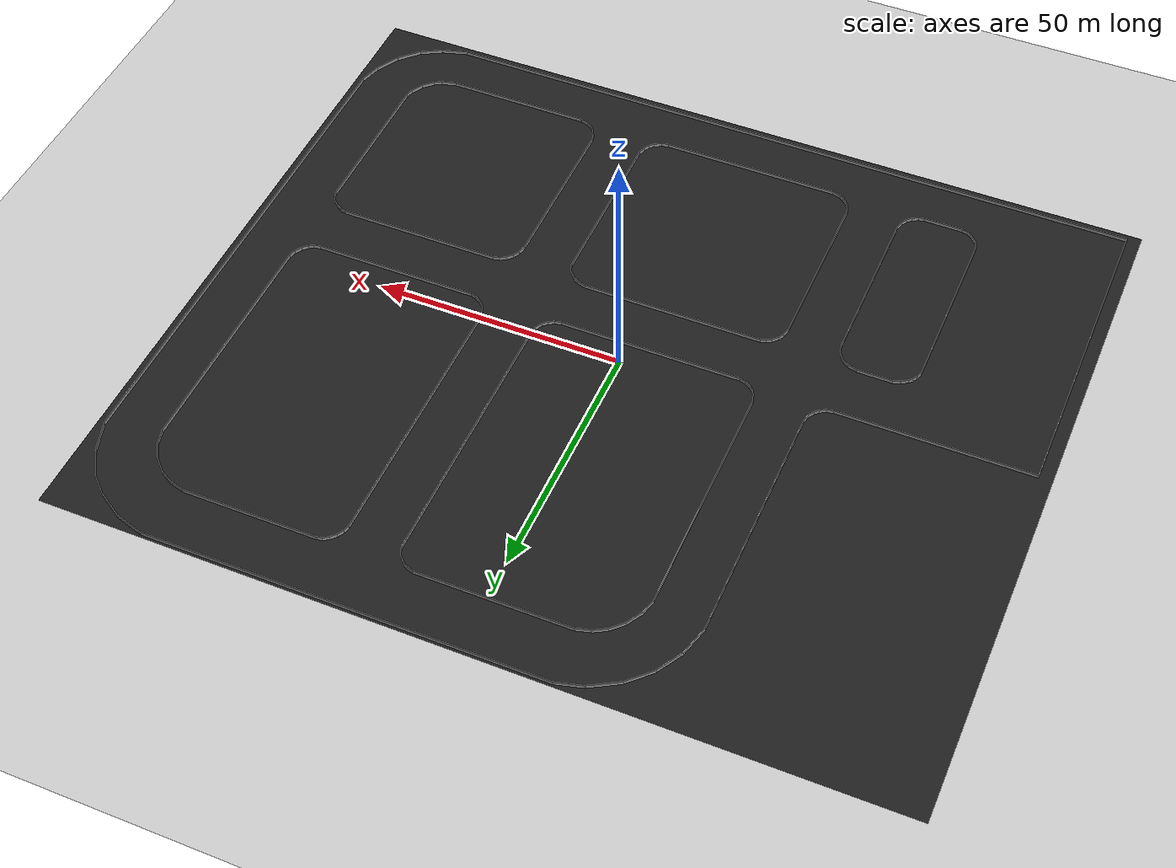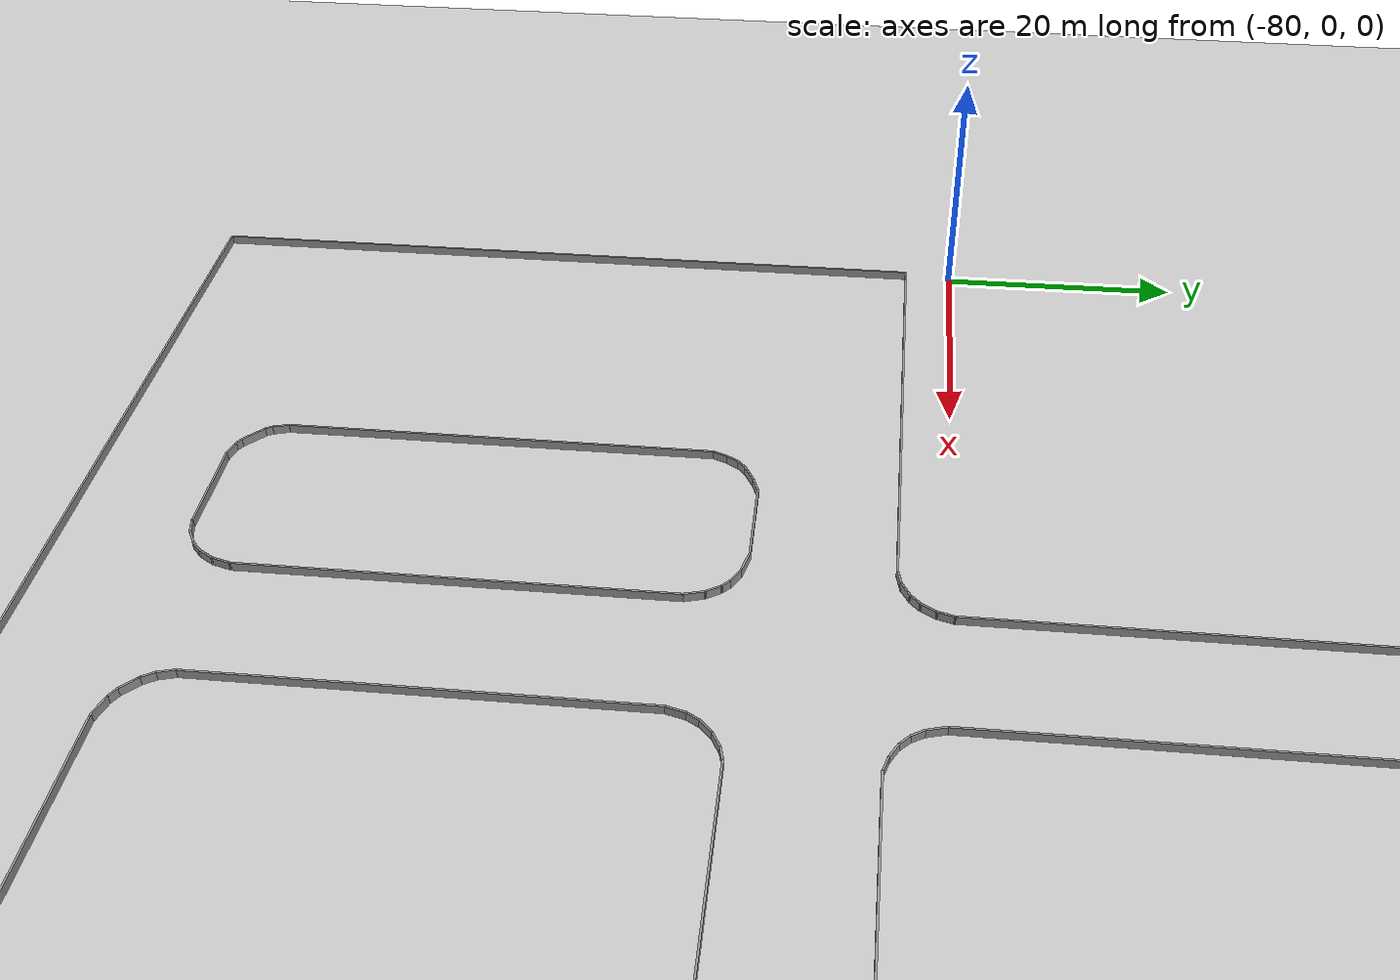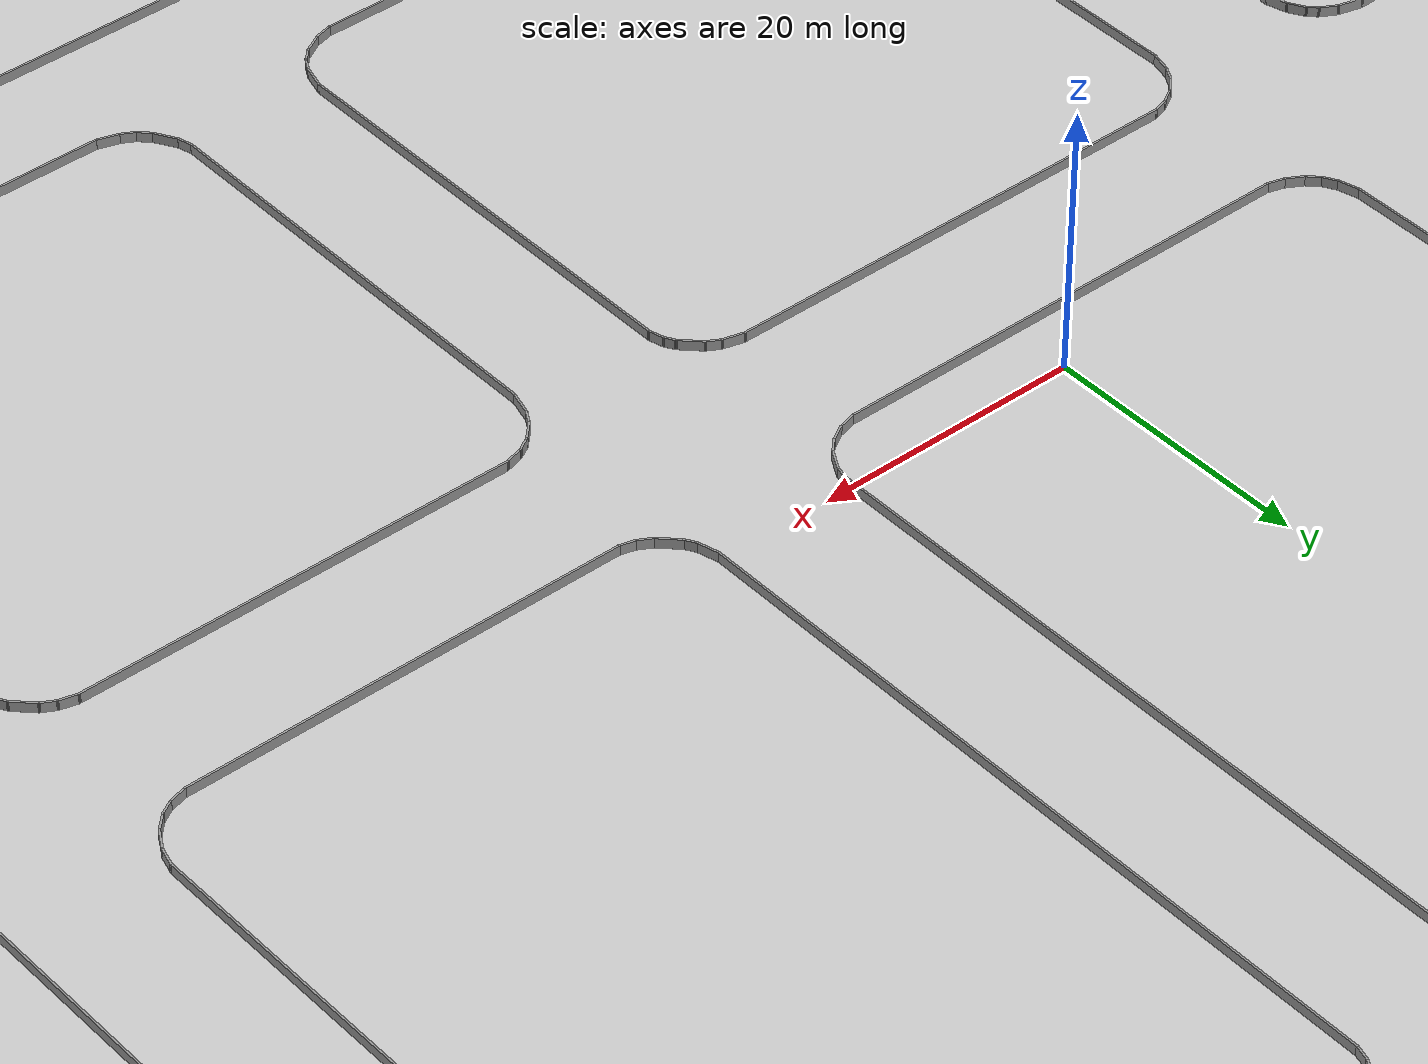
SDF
<sdf version="1.6">
 <world name="default">
  <scene>
   <ambient>0 0 0 1</ambient>
   <shadows>0</shadows>
   <grid>0</grid>
   <background>0.7 0.7 0.7 1</background>
  </scene>
  <model name="course">
   <static>1</static>
   <link name="course_link">
    <collision name="course_collision">
     <geometry><plane><normal>0 0 1</normal><size>152.72 129.83</size></plane></geometry>
     <surface><friction><ode><mu>100</mu><mu2>50</mu2></ode></friction></surface>
    </collision>
    <visual name="course_visual">
     <cast_shadows>0</cast_shadows>
     <geometry><plane><normal>0 0 1</normal><size>152.72 129.83</size></plane></geometry>
     <material>
      <script>
       <uri>model://isaretler/course/materials/scripts</uri>
       <uri>model://isaretler/course/materials/textures</uri>
       <name>course</name>
      </script>
     </material>
    </visual>
   </link>
  </model>
  <model name="ground2">
   <pose>-0.060291 -0.062788 -0.180139 0 -0 0</pose>
   <static>1</static>
   <link name="ground">
    <collision name="ground_coll"><geometry><box><size>165 140 0.01</size></box></geometry></collision>
    <visual name="ground_vis">
     <geometry><box><size>165 140 0.01</size></box></geometry>
     <material>
      <script><uri>file://media/materials/scripts/gazebo.material</uri><name>Gazebo/FlatBlack</name></script>
     </material>
    </visual>
   </link>
  </model>
  <gravity>0 0 -9.8</gravity>
  <magnetic_field>6e-06 2.3e-05 -4.2e-05</magnetic_field>
  <atmosphere type="adiabatic"/>
  <physics name="default_physics" default="0" type="ode">
   <max_step_size>0.001</max_step_size>
   <real_time_factor>1</real_time_factor>
   <real_time_update_rate>1000</real_time_update_rate>
  </physics>
  <spherical_coordinates>
   <surface_model>EARTH_WGS84</surface_model>
   <latitude_deg>0</latitude_deg>
   <longitude_deg>0</longitude_deg>
   <elevation>0</elevation>
   <heading_deg>0</heading_deg>
  </spherical_coordinates>
  <light name="some_light" type="directional">
   <diffuse>1 1 1 1</diffuse>
   <specular>1 1 1 0</specular>
   <direction>-1 -1 -1</direction>
  </light>
  <model name="Ic_Duvarlar">
   <pose>8.43 0.0842 0 0 -0 0</pose>
   <link name="Wall_0">
    <collision name="Wall_0_Collision">
     <geometry><box><size>35.25 0.15 0.75</size></box></geometry>
     <pose>0 0 0.375 0 -0 0</pose>
    </collision>
    <visual name="Wall_0_Visual">
     <pose>0 0 0.375 0 -0 0</pose>
     <geometry><box><size>35.25 0.15 0.75</size></box></geometry>
     <material>
      <script><uri>file://media/materials/scripts/gazebo.material</uri><name>Gazebo/Grey</name></script>
      <ambient>1 1 1 1</ambient>
     </material>
    </visual>
    <pose>-61.5911 -36.6736 0 0 0 -1.5708</pose>
   </link>
   <link name="Wall_1">
    <collision name="Wall_1_Collision">
     <geometry><box><size>1.5 0.15 0.75</size></box></geometry>
     <pose>0 0 0.375 0 -0 0</pose>
    </collision>
    <visual name="Wall_1_Visual">
     <pose>0 0 0.375 0 -0 0</pose>
     <geometry><box><size>1.5 0.15 0.75</size></box></geometry>
     <material>
      <script><uri>file://media/materials/scripts/gazebo.material</uri><name>Gazebo/Grey</name></script>
      <ambient>1 1 1 1</ambient>
     </material>
    </visual>
    <pose>-61.4162 -54.8756 0 0 0 -1.30857</pose>
   </link>
   <link name="Wall_101">
    <collision name="Wall_101_Collision">
     <geometry><box><size>1.5 0.15 0.75</size></box></geometry>
     <pose>0 0 0.375 0 -0 0</pose>
    </collision>
    <visual name="Wall_101_Visual">
     <pose>0 0 0.375 0 -0 0</pose>
     <geometry><box><size>1.5 0.15 0.75</size></box></geometry>
     <material>
      <script><uri>file://media/materials/scripts/gazebo.material</uri><name>Gazebo/Grey</name></script>
      <ambient>1 1 1 1</ambient>
     </material>
    </visual>
    <pose>6.14385 58.0924 0 0 -0 2.87937</pose>
   </link>
   <link name="Wall_102">
    <collision name="Wall_102_Collision">
     <geometry><box><size>30.5 0.15 0.75</size></box></geometry>
     <pose>0 0 0.375 0 -0 0</pose>
    </collision>
    <visual name="Wall_102_Visual">
     <pose>0 0 0.375 0 -0 0</pose>
     <geometry><box><size>30.5 0.15 0.75</size></box></geometry>
     <material>
      <script><uri>file://media/materials/scripts/gazebo.material</uri><name>Gazebo/Grey</name></script>
      <ambient>1 1 1 1</ambient>
     </material>
    </visual>
    <pose>-9.68315 58.2674 0 0 -0 3.14159</pose>
   </link>
   <link name="Wall_107">
    <collision name="Wall_107_Collision">
     <geometry><box><size>3.25 0.15 0.75</size></box></geometry>
     <pose>0 0 0.375 0 -0 0</pose>
    </collision>
    <visual name="Wall_107_Visual">
     <pose>0 0 0.375 0 -0 0</pose>
     <geometry><box><size>3.25 0.15 0.75</size></box></geometry>
     <material>
      <script><uri>file://media/materials/scripts/gazebo.material</uri><name>Gazebo/Grey</name></script>
      <ambient>1 1 1 1</ambient>
     </material>
    </visual>
    <pose>-26.3557 57.8659 0 0 0 -2.87964</pose>
   </link>
   <link name="Wall_108">
    <collision name="Wall_108_Collision">
     <geometry><box><size>3 0.15 0.75</size></box></geometry>
     <pose>0 0 0.375 0 -0 0</pose>
    </collision>
    <visual name="Wall_108_Visual">
     <pose>0 0 0.375 0 -0 0</pose>
     <geometry><box><size>3 0.15 0.75</size></box></geometry>
     <material>
      <script><uri>file://media/materials/scripts/gazebo.material</uri><name>Gazebo/Grey</name></script>
      <ambient>1 1 1 1</ambient>
     </material>
    </visual>
    <pose>-29.0872 56.7519 0 0 0 -2.61796</pose>
   </link>
   <link name="Wall_110">
    <collision name="Wall_110_Collision">
     <geometry><box><size>3.25 0.15 0.75</size></box></geometry>
     <pose>0 0 0.375 0 -0 0</pose>
    </collision>
    <visual name="Wall_110_Visual">
     <pose>0 0 0.375 0 -0 0</pose>
     <geometry><box><size>3.25 0.15 0.75</size></box></geometry>
     <material>
      <script><uri>file://media/materials/scripts/gazebo.material</uri><name>Gazebo/Grey</name></script>
      <ambient>1 1 1 1</ambient>
     </material>
    </visual>
    <pose>-31.4172 54.9434 0 0 0 -2.35619</pose>
   </link>
   <link name="Wall_111">
    <collision name="Wall_111_Collision">
     <geometry><box><size>3.75 0.15 0.75</size></box></geometry>
     <pose>0 0 0.375 0 -0 0</pose>
    </collision>
    <visual name="Wall_111_Visual">
     <pose>0 0 0.375 0 -0 0</pose>
     <geometry><box><size>3.75 0.15 0.75</size></box></geometry>
     <material>
      <script><uri>file://media/materials/scripts/gazebo.material</uri><name>Gazebo/Grey</name></script>
      <ambient>1 1 1 1</ambient>
     </material>
    </visual>
    <pose>-33.4132 52.2889 0 0 0 -2.09449</pose>
   </link>
   <link name="Wall_113">
    <collision name="Wall_113_Collision">
     <geometry><box><size>3 0.15 0.75</size></box></geometry>
     <pose>0 0 0.375 0 -0 0</pose>
    </collision>
    <visual name="Wall_113_Visual">
     <pose>0 0 0.375 0 -0 0</pose>
     <geometry><box><size>3 0.15 0.75</size></box></geometry>
     <material>
      <script><uri>file://media/materials/scripts/gazebo.material</uri><name>Gazebo/Grey</name></script>
      <ambient>1 1 1 1</ambient>
     </material>
    </visual>
    <pose>-34.6817 49.3539 0 0 0 -1.83237</pose>
   </link>
   <link name="Wall_115">
    <collision name="Wall_115_Collision">
     <geometry><box><size>48.5 0.15 0.75</size></box></geometry>
     <pose>0 0 0.375 0 -0 0</pose>
    </collision>
    <visual name="Wall_115_Visual">
     <pose>0 0 0.375 0 -0 0</pose>
     <geometry><box><size>48.5 0.15 0.75</size></box></geometry>
     <material>
      <script><uri>file://media/materials/scripts/gazebo.material</uri><name>Gazebo/Grey</name></script>
      <ambient>1 1 1 1</ambient>
     </material>
    </visual>
    <pose>-35.0502 23.8024 0 0 0 -1.5708</pose>
   </link>
   <link name="Wall_116">
    <collision name="Wall_116_Collision">
     <geometry><box><size>1.75 0.15 0.75</size></box></geometry>
     <pose>0 0 0.375 0 -0 0</pose>
    </collision>
    <visual name="Wall_116_Visual">
     <pose>0 0 0.375 0 -0 0</pose>
     <geometry><box><size>1.75 0.15 0.75</size></box></geometry>
     <material>
      <script><uri>file://media/materials/scripts/gazebo.material</uri><name>Gazebo/Grey</name></script>
      <ambient>1 1 1 1</ambient>
     </material>
    </visual>
    <pose>-34.8432 -1.14562 0 0 0 -1.30915</pose>
   </link>
   <link name="Wall_117">
    <collision name="Wall_117_Collision">
     <geometry><box><size>1.25 0.15 0.75</size></box></geometry>
     <pose>0 0 0.375 0 -0 0</pose>
    </collision>
    <visual name="Wall_117_Visual">
     <pose>0 0 0.375 0 -0 0</pose>
     <geometry><box><size>1.25 0.15 0.75</size></box></geometry>
     <material>
      <script><uri>file://media/materials/scripts/gazebo.material</uri><name>Gazebo/Grey</name></script>
      <ambient>1 1 1 1</ambient>
     </material>
    </visual>
    <pose>-34.3612 -2.39461 0 0 0 -1.04691</pose>
   </link>
   <link name="Wall_118">
    <collision name="Wall_118_Collision">
     <geometry><box><size>1.25 0.15 0.75</size></box></geometry>
     <pose>0 0 0.375 0 -0 0</pose>
    </collision>
    <visual name="Wall_118_Visual">
     <pose>0 0 0.375 0 -0 0</pose>
     <geometry><box><size>1.25 0.15 0.75</size></box></geometry>
     <material>
      <script><uri>file://media/materials/scripts/gazebo.material</uri><name>Gazebo/Grey</name></script>
      <ambient>1 1 1 1</ambient>
     </material>
    </visual>
    <pose>-33.6972 -3.25962 0 0 0 -0.785398</pose>
   </link>
   <link name="Wall_120">
    <collision name="Wall_120_Collision">
     <geometry><box><size>1.39796 0.15 0.75</size></box></geometry>
     <pose>0 0 0.375 0 -0 0</pose>
    </collision>
    <visual name="Wall_120_Visual">
     <pose>0 0 0.375 0 -0 0</pose>
     <geometry><box><size>1.39796 0.15 0.75</size></box></geometry>
     <material>
      <script><uri>file://media/materials/scripts/gazebo.material</uri><name>Gazebo/Grey</name></script>
      <ambient>1 1 1 1</ambient>
     </material>
    </visual>
    <pose>-31.5427 -4.50662 0 0 0 -0.297674</pose>
   </link>
   <link name="Wall_122">
    <collision name="Wall_122_Collision">
     <geometry><box><size>33 0.15 0.75</size></box></geometry>
     <pose>0 0 0.375 0 -0 0</pose>
    </collision>
    <visual name="Wall_122_Visual">
     <pose>0 0 0.375 0 -0 0</pose>
     <geometry><box><size>33 0.15 0.75</size></box></geometry>
     <material>
      <script><uri>file://media/materials/scripts/gazebo.material</uri><name>Gazebo/Grey</name></script>
      <ambient>1 1 1 1</ambient>
     </material>
    </visual>
    <pose>40.8108 -4.68461 0 0 -0 0</pose>
   </link>
   <link name="Wall_123">
    <collision name="Wall_123_Collision">
     <geometry><box><size>1.5 0.15 0.75</size></box></geometry>
     <pose>0 0 0.375 0 -0 0</pose>
    </collision>
    <visual name="Wall_123_Visual">
     <pose>0 0 0.375 0 -0 0</pose>
     <geometry><box><size>1.5 0.15 0.75</size></box></geometry>
     <material>
      <script><uri>file://media/materials/scripts/gazebo.material</uri><name>Gazebo/Grey</name></script>
      <ambient>1 1 1 1</ambient>
     </material>
    </visual>
    <pose>57.8879 -4.51011 0 0 -0 0.261509</pose>
   </link>
   <link name="Wall_124">
    <collision name="Wall_124_Collision">
     <geometry><box><size>1.25 0.15 0.75</size></box></geometry>
     <pose>0 0 0.375 0 -0 0</pose>
    </collision>
    <visual name="Wall_124_Visual">
     <pose>0 0 0.375 0 -0 0</pose>
     <geometry><box><size>1.25 0.15 0.75</size></box></geometry>
     <material>
      <script><uri>file://media/materials/scripts/gazebo.material</uri><name>Gazebo/Grey</name></script>
      <ambient>1 1 1 1</ambient>
     </material>
    </visual>
    <pose>59.0164 -4.06062 0 0 -0 0.52343</pose>
   </link>
   <link name="Wall_125">
    <collision name="Wall_125_Collision">
     <geometry><box><size>1.5 0.15 0.75</size></box></geometry>
     <pose>0 0 0.375 0 -0 0</pose>
    </collision>
    <visual name="Wall_125_Visual">
     <pose>0 0 0.375 0 -0 0</pose>
     <geometry><box><size>1.5 0.15 0.75</size></box></geometry>
     <material>
      <script><uri>file://media/materials/scripts/gazebo.material</uri><name>Gazebo/Grey</name></script>
      <ambient>1 1 1 1</ambient>
     </material>
    </visual>
    <pose>59.9703 -3.30811 0 0 -0 0.785398</pose>
   </link>
   <link name="Wall_126">
    <collision name="Wall_126_Collision">
     <geometry><box><size>1.75 0.15 0.75</size></box></geometry>
     <pose>0 0 0.375 0 -0 0</pose>
    </collision>
    <visual name="Wall_126_Visual">
     <pose>0 0 0.375 0 -0 0</pose>
     <geometry><box><size>1.75 0.15 0.75</size></box></geometry>
     <material>
      <script><uri>file://media/materials/scripts/gazebo.material</uri><name>Gazebo/Grey</name></script>
      <ambient>1 1 1 1</ambient>
     </material>
    </visual>
    <pose>60.8478 -2.13811 0 0 -0 1.047</pose>
   </link>
   <link name="Wall_130">
    <collision name="Wall_130_Collision">
     <geometry><box><size>1.5 0.15 0.75</size></box></geometry>
     <pose>0 0 0.375 0 -0 0</pose>
    </collision>
    <visual name="Wall_130_Visual">
     <pose>0 0 0.375 0 -0 0</pose>
     <geometry><box><size>1.5 0.15 0.75</size></box></geometry>
     <material>
      <script><uri>file://media/materials/scripts/gazebo.material</uri><name>Gazebo/Grey</name></script>
      <ambient>1 1 1 1</ambient>
     </material>
    </visual>
    <pose>61.4224 -0.793615 0 0 -0 1.30929</pose>
   </link>
   <link name="Wall_131">
    <collision name="Wall_131_Collision">
     <geometry><box><size>48.25 0.15 0.75</size></box></geometry>
     <pose>0 0 0.375 0 -0 0</pose>
    </collision>
    <visual name="Wall_131_Visual">
     <pose>0 0 0.375 0 -0 0</pose>
     <geometry><box><size>48.25 0.15 0.75</size></box></geometry>
     <material>
      <script><uri>file://media/materials/scripts/gazebo.material</uri><name>Gazebo/Grey</name></script>
      <ambient>1 1 1 1</ambient>
     </material>
    </visual>
    <pose>61.5968 23.9084 0 0 -0 1.5708</pose>
   </link>
   <link name="Wall_132">
    <collision name="Wall_132_Collision">
     <geometry><box><size>3 0.15 0.75</size></box></geometry>
     <pose>0 0 0.375 0 -0 0</pose>
    </collision>
    <visual name="Wall_132_Visual">
     <pose>0 0 0.375 0 -0 0</pose>
     <geometry><box><size>3 0.15 0.75</size></box></geometry>
     <material>
      <script><uri>file://media/materials/scripts/gazebo.material</uri><name>Gazebo/Grey</name></script>
      <ambient>1 1 1 1</ambient>
     </material>
    </visual>
    <pose>61.2278 49.3349 0 0 -0 1.83271</pose>
   </link>
   <link name="Wall_133">
    <collision name="Wall_133_Collision">
     <geometry><box><size>3.5 0.15 0.75</size></box></geometry>
     <pose>0 0 0.375 0 -0 0</pose>
    </collision>
    <visual name="Wall_133_Visual">
     <pose>0 0 0.375 0 -0 0</pose>
     <geometry><box><size>3.5 0.15 0.75</size></box></geometry>
     <material>
      <script><uri>file://media/materials/scripts/gazebo.material</uri><name>Gazebo/Grey</name></script>
      <ambient>1 1 1 1</ambient>
     </material>
    </visual>
    <pose>60.0213 52.1624 0 0 -0 2.09427</pose>
   </link>
   <link name="Wall_134">
    <collision name="Wall_134_Collision">
     <geometry><box><size>3.75 0.15 0.75</size></box></geometry>
     <pose>0 0 0.375 0 -0 0</pose>
    </collision>
    <visual name="Wall_134_Visual">
     <pose>0 0 0.375 0 -0 0</pose>
     <geometry><box><size>3.75 0.15 0.75</size></box></geometry>
     <material>
      <script><uri>file://media/materials/scripts/gazebo.material</uri><name>Gazebo/Grey</name></script>
      <ambient>1 1 1 1</ambient>
     </material>
    </visual>
    <pose>57.9113 54.8859 0 0 -0 2.35619</pose>
   </link>
   <link name="Wall_135">
    <collision name="Wall_135_Collision">
     <geometry><box><size>2.75 0.15 0.75</size></box></geometry>
     <pose>0 0 0.375 0 -0 0</pose>
    </collision>
    <visual name="Wall_135_Visual">
     <pose>0 0 0.375 0 -0 0</pose>
     <geometry><box><size>2.75 0.15 0.75</size></box></geometry>
     <material>
      <script><uri>file://media/materials/scripts/gazebo.material</uri><name>Gazebo/Grey</name></script>
      <ambient>1 1 1 1</ambient>
     </material>
    </visual>
    <pose>55.5129 56.8084 0 0 -0 2.61806</pose>
   </link>
   <link name="Wall_136">
    <collision name="Wall_136_Collision">
     <geometry><box><size>3.5 0.15 0.75</size></box></geometry>
     <pose>0 0 0.375 0 -0 0</pose>
    </collision>
    <visual name="Wall_136_Visual">
     <pose>0 0 0.375 0 -0 0</pose>
     <geometry><box><size>3.5 0.15 0.75</size></box></geometry>
     <material>
      <script><uri>file://media/materials/scripts/gazebo.material</uri><name>Gazebo/Grey</name></script>
      <ambient>1 1 1 1</ambient>
     </material>
    </visual>
    <pose>52.7688 57.8919 0 0 -0 2.87982</pose>
   </link>
   <link name="Wall_137">
    <collision name="Wall_137_Collision">
     <geometry><box><size>27.01 0.15 0.75</size></box></geometry>
     <pose>0 0 0.375 0 -0 0</pose>
    </collision>
    <visual name="Wall_137_Visual">
     <pose>0 0 0.375 0 -0 0</pose>
     <geometry><box><size>27.01 0.15 0.75</size></box></geometry>
     <material>
      <script><uri>file://media/materials/scripts/gazebo.material</uri><name>Gazebo/Grey</name></script>
      <ambient>1 1 1 1</ambient>
     </material>
    </visual>
    <pose>37.7208 58.3254 0 0 -0 3.14159</pose>
   </link>
   <link name="Wall_138">
    <collision name="Wall_138_Collision">
     <geometry><box><size>1.24002 0.15 0.75</size></box></geometry>
     <pose>0 0 0.375 0 -0 0</pose>
    </collision>
    <visual name="Wall_138_Visual">
     <pose>0 0 0.375 0 -0 0</pose>
     <geometry><box><size>1.24002 0.15 0.75</size></box></geometry>
     <material>
      <script><uri>file://media/materials/scripts/gazebo.material</uri><name>Gazebo/Grey</name></script>
      <ambient>1 1 1 1</ambient>
     </material>
    </visual>
    <pose>23.7648 58.1829 0 0 0 -2.87703</pose>
   </link>
   <link name="Wall_139">
    <collision name="Wall_139_Collision">
     <geometry><box><size>1.25 0.15 0.75</size></box></geometry>
     <pose>0 0 0.375 0 -0 0</pose>
    </collision>
    <visual name="Wall_139_Visual">
     <pose>0 0 0.375 0 -0 0</pose>
     <geometry><box><size>1.25 0.15 0.75</size></box></geometry>
     <material>
      <script><uri>file://media/materials/scripts/gazebo.material</uri><name>Gazebo/Grey</name></script>
      <ambient>1 1 1 1</ambient>
     </material>
    </visual>
    <pose>22.7624 57.7654 0 0 0 -2.61816</pose>
   </link>
   <link name="Wall_14">
    <collision name="Wall_14_Collision">
     <geometry><box><size>34.25 0.15 0.75</size></box></geometry>
     <pose>0 0 0.375 0 -0 0</pose>
    </collision>
    <visual name="Wall_14_Visual">
     <pose>0 0 0.375 0 -0 0</pose>
     <geometry><box><size>34.25 0.15 0.75</size></box></geometry>
     <material>
      <script><uri>file://media/materials/scripts/gazebo.material</uri><name>Gazebo/Grey</name></script>
      <ambient>1 1 1 1</ambient>
     </material>
    </visual>
    <pose>-45.6142 -36.6996 0 0 -0 1.5708</pose>
   </link>
   <link name="Wall_140">
    <collision name="Wall_140_Collision">
     <geometry><box><size>1.75 0.15 0.75</size></box></geometry>
     <pose>0 0 0.375 0 -0 0</pose>
    </collision>
    <visual name="Wall_140_Visual">
     <pose>0 0 0.375 0 -0 0</pose>
     <geometry><box><size>1.75 0.15 0.75</size></box></geometry>
     <material>
      <script><uri>file://media/materials/scripts/gazebo.material</uri><name>Gazebo/Grey</name></script>
      <ambient>1 1 1 1</ambient>
     </material>
    </visual>
    <pose>21.7203 56.9249 0 0 0 -2.35619</pose>
   </link>
   <link name="Wall_141">
    <collision name="Wall_141_Collision">
     <geometry><box><size>1.54049 0.15 0.75</size></box></geometry>
     <pose>0 0 0.375 0 -0 0</pose>
    </collision>
    <visual name="Wall_141_Visual">
     <pose>0 0 0.375 0 -0 0</pose>
     <geometry><box><size>1.54049 0.15 0.75</size></box></geometry>
     <material>
      <script><uri>file://media/materials/scripts/gazebo.material</uri><name>Gazebo/Grey</name></script>
      <ambient>1 1 1 1</ambient>
     </material>
    </visual>
    <pose>20.8173 55.7514 0 0 0 -2.07755</pose>
   </link>
   <link name="Wall_142">
    <collision name="Wall_142_Collision">
     <geometry><box><size>1.22717 0.15 0.75</size></box></geometry>
     <pose>0 0 0.375 0 -0 0</pose>
    </collision>
    <visual name="Wall_142_Visual">
     <pose>0 0 0.375 0 -0 0</pose>
     <geometry><box><size>1.22717 0.15 0.75</size></box></geometry>
     <material>
      <script><uri>file://media/materials/scripts/gazebo.material</uri><name>Gazebo/Grey</name></script>
      <ambient>1 1 1 1</ambient>
     </material>
    </visual>
    <pose>20.3373 54.6239 0 0 0 -1.83851</pose>
   </link>
   <link name="Wall_144">
    <collision name="Wall_144_Collision">
     <geometry><box><size>54.5 0.15 0.75</size></box></geometry>
     <pose>0 0 0.375 0 -0 0</pose>
    </collision>
    <visual name="Wall_144_Visual">
     <pose>0 0 0.375 0 -0 0</pose>
     <geometry><box><size>54.5 0.15 0.75</size></box></geometry>
     <material>
      <script><uri>file://media/materials/scripts/gazebo.material</uri><name>Gazebo/Grey</name></script>
      <ambient>1 1 1 1</ambient>
     </material>
    </visual>
    <pose>20.1948 26.9294 0 0 0 -1.5708</pose>
   </link>
   <link name="Wall_145">
    <collision name="Wall_145_Collision">
     <geometry><box><size>1.75 0.15 0.75</size></box></geometry>
     <pose>0 0 0.375 0 -0 0</pose>
    </collision>
    <visual name="Wall_145_Visual">
     <pose>0 0 0.375 0 -0 0</pose>
     <geometry><box><size>1.75 0.15 0.75</size></box></geometry>
     <material>
      <script><uri>file://media/materials/scripts/gazebo.material</uri><name>Gazebo/Grey</name></script>
      <ambient>1 1 1 1</ambient>
     </material>
    </visual>
    <pose>20.4018 -1.01812 0 0 0 -1.30899</pose>
   </link>
   <link name="Wall_146">
    <collision name="Wall_146_Collision">
     <geometry><box><size>1 0.15 0.75</size></box></geometry>
     <pose>0 0 0.375 0 -0 0</pose>
    </collision>
    <visual name="Wall_146_Visual">
     <pose>0 0 0.375 0 -0 0</pose>
     <geometry><box><size>1 0.15 0.75</size></box></geometry>
     <material>
      <script><uri>file://media/materials/scripts/gazebo.material</uri><name>Gazebo/Grey</name></script>
      <ambient>1 1 1 1</ambient>
     </material>
    </visual>
    <pose>20.8213 -2.15862 0 0 0 -1.04713</pose>
   </link>
   <link name="Wall_147">
    <collision name="Wall_147_Collision">
     <geometry><box><size>2 0.15 0.75</size></box></geometry>
     <pose>0 0 0.375 0 -0 0</pose>
    </collision>
    <visual name="Wall_147_Visual">
     <pose>0 0 0.375 0 -0 0</pose>
     <geometry><box><size>2 0.15 0.75</size></box></geometry>
     <material>
      <script><uri>file://media/materials/scripts/gazebo.material</uri><name>Gazebo/Grey</name></script>
      <ambient>1 1 1 1</ambient>
     </material>
    </visual>
    <pose>21.6878 -3.18112 0 0 0 -0.78578</pose>
   </link>
   <link name="Wall_148">
    <collision name="Wall_148_Collision">
     <geometry><box><size>1.25 0.15 0.75</size></box></geometry>
     <pose>0 0 0.375 0 -0 0</pose>
    </collision>
    <visual name="Wall_148_Visual">
     <pose>0 0 0.375 0 -0 0</pose>
     <geometry><box><size>1.25 0.15 0.75</size></box></geometry>
     <material>
      <script><uri>file://media/materials/scripts/gazebo.material</uri><name>Gazebo/Grey</name></script>
      <ambient>1 1 1 1</ambient>
     </material>
    </visual>
    <pose>22.8183 -4.11062 0 0 0 -0.52343</pose>
   </link>
   <link name="Wall_149">
    <collision name="Wall_149_Collision">
     <geometry><box><size>1.28182 0.15 0.75</size></box></geometry>
     <pose>0 0 0.375 0 -0 0</pose>
    </collision>
    <visual name="Wall_149_Visual">
     <pose>0 0 0.375 0 -0 0</pose>
     <geometry><box><size>1.28182 0.15 0.75</size></box></geometry>
     <material>
      <script><uri>file://media/materials/scripts/gazebo.material</uri><name>Gazebo/Grey</name></script>
      <ambient>1 1 1 1</ambient>
     </material>
    </visual>
    <pose>23.8403 -4.53512 0 0 0 -0.267493</pose>
   </link>
   <link name="Wall_15">
    <collision name="Wall_15_Collision">
     <geometry><box><size>1.75 0.15 0.75</size></box></geometry>
     <pose>0 0 0.375 0 -0 0</pose>
    </collision>
    <visual name="Wall_15_Visual">
     <pose>0 0 0.375 0 -0 0</pose>
     <geometry><box><size>1.75 0.15 0.75</size></box></geometry>
     <material>
      <script><uri>file://media/materials/scripts/gazebo.material</uri><name>Gazebo/Grey</name></script>
      <ambient>1 1 1 1</ambient>
     </material>
    </visual>
    <pose>-45.8212 -18.8771 0 0 -0 1.83261</pose>
   </link>
   <link name="Wall_151">
    <collision name="Wall_151_Collision">
     <geometry><box><size>1.75 0.15 0.75</size></box></geometry>
     <pose>0 0 0.375 0 -0 0</pose>
    </collision>
    <visual name="Wall_151_Visual">
     <pose>0 0 0.375 0 -0 0</pose>
     <geometry><box><size>1.75 0.15 0.75</size></box></geometry>
     <material>
      <script><uri>file://media/materials/scripts/gazebo.material</uri><name>Gazebo/Grey</name></script>
      <ambient>1 1 1 1</ambient>
     </material>
    </visual>
    <pose>-45.8212 -54.5226 0 0 0 -1.83245</pose>
   </link>
   <link name="Wall_154">
    <collision name="Wall_154_Collision">
     <geometry><box><size>1.5 0.15 0.75</size></box></geometry>
     <pose>0 0 0.375 0 -0 0</pose>
    </collision>
    <visual name="Wall_154_Visual">
     <pose>0 0 0.375 0 -0 0</pose>
     <geometry><box><size>1.5 0.15 0.75</size></box></geometry>
     <material>
      <script><uri>file://media/materials/scripts/gazebo.material</uri><name>Gazebo/Grey</name></script>
      <ambient>1 1 1 1</ambient>
     </material>
    </visual>
    <pose>-46.3657 -55.8801 0 0 0 -2.09444</pose>
   </link>
   <link name="Wall_155">
    <collision name="Wall_155_Collision">
     <geometry><box><size>1.25 0.15 0.75</size></box></geometry>
     <pose>0 0 0.375 0 -0 0</pose>
    </collision>
    <visual name="Wall_155_Visual">
     <pose>0 0 0.375 0 -0 0</pose>
     <geometry><box><size>1.25 0.15 0.75</size></box></geometry>
     <material>
      <script><uri>file://media/materials/scripts/gazebo.material</uri><name>Gazebo/Grey</name></script>
      <ambient>1 1 1 1</ambient>
     </material>
    </visual>
    <pose>-47.0922 -56.8536 0 0 0 -2.35619</pose>
   </link>
   <link name="Wall_156">
    <collision name="Wall_156_Collision">
     <geometry><box><size>1.5 0.15 0.75</size></box></geometry>
     <pose>0 0 0.375 0 -0 0</pose>
    </collision>
    <visual name="Wall_156_Visual">
     <pose>0 0 0.375 0 -0 0</pose>
     <geometry><box><size>1.5 0.15 0.75</size></box></geometry>
     <material>
      <script><uri>file://media/materials/scripts/gazebo.material</uri><name>Gazebo/Grey</name></script>
      <ambient>1 1 1 1</ambient>
     </material>
    </visual>
    <pose>-48.0657 -57.5801 0 0 0 -2.61794</pose>
   </link>
   <link name="Wall_157">
    <collision name="Wall_157_Collision">
     <geometry><box><size>1.31354 0.15 0.75</size></box></geometry>
     <pose>0 0 0.375 0 -0 0</pose>
    </collision>
    <visual name="Wall_157_Visual">
     <pose>0 0 0.375 0 -0 0</pose>
     <geometry><box><size>1.31354 0.15 0.75</size></box></geometry>
     <material>
      <script><uri>file://media/materials/scripts/gazebo.material</uri><name>Gazebo/Grey</name></script>
      <ambient>1 1 1 1</ambient>
     </material>
    </visual>
    <pose>-49.2167 -58.0496 0 0 0 -2.91267</pose>
   </link>
   <link name="Wall_159">
    <collision name="Wall_159_Collision">
     <geometry><box><size>1 0.15 0.75</size></box></geometry>
     <pose>0 0 0.375 0 -0 0</pose>
    </collision>
    <visual name="Wall_159_Visual">
     <pose>0 0 0.375 0 -0 0</pose>
     <geometry><box><size>1 0.15 0.75</size></box></geometry>
     <material>
      <script><uri>file://media/materials/scripts/gazebo.material</uri><name>Gazebo/Grey</name></script>
      <ambient>1 1 1 1</ambient>
     </material>
    </visual>
    <pose>-60.2856 -16.7421 0 0 -0 0.785398</pose>
   </link>
   <link name="Wall_16">
    <collision name="Wall_16_Collision">
     <geometry><box><size>1.5 0.15 0.75</size></box></geometry>
     <pose>0 0 0.375 0 -0 0</pose>
    </collision>
    <visual name="Wall_16_Visual">
     <pose>0 0 0.375 0 -0 0</pose>
     <geometry><box><size>1.5 0.15 0.75</size></box></geometry>
     <material>
      <script><uri>file://media/materials/scripts/gazebo.material</uri><name>Gazebo/Grey</name></script>
      <ambient>1 1 1 1</ambient>
     </material>
    </visual>
    <pose>-46.3657 -17.5201 0 0 -0 2.09444</pose>
   </link>
   <link name="Wall_160">
    <collision name="Wall_160_Collision">
     <geometry><box><size>1.75 0.15 0.75</size></box></geometry>
     <pose>0 0 0.375 0 -0 0</pose>
    </collision>
    <visual name="Wall_160_Visual">
     <pose>0 0 0.375 0 -0 0</pose>
     <geometry><box><size>1.75 0.15 0.75</size></box></geometry>
     <material>
      <script><uri>file://media/materials/scripts/gazebo.material</uri><name>Gazebo/Grey</name></script>
      <ambient>1 1 1 1</ambient>
     </material>
    </visual>
    <pose>-59.2921 -16.0416 0 0 -0 0.523487</pose>
   </link>
   <link name="Wall_161">
    <collision name="Wall_161_Collision">
     <geometry><box><size>1.47243 0.15 0.75</size></box></geometry>
     <pose>0 0 0.375 0 -0 0</pose>
    </collision>
    <visual name="Wall_161_Visual">
     <pose>0 0 0.375 0 -0 0</pose>
     <geometry><box><size>1.47243 0.15 0.75</size></box></geometry>
     <material>
      <script><uri>file://media/materials/scripts/gazebo.material</uri><name>Gazebo/Grey</name></script>
      <ambient>1 1 1 1</ambient>
     </material>
    </visual>
    <pose>-57.9796 -15.4111 0 0 -0 0.356203</pose>
   </link>
   <link name="Wall_163">
    <collision name="Wall_163_Collision">
     <geometry><box><size>1.50015 0.15 0.75</size></box></geometry>
     <pose>0 0 0.375 0 -0 0</pose>
    </collision>
    <visual name="Wall_163_Visual">
     <pose>0 0 0.375 0 -0 0</pose>
     <geometry><box><size>1.50015 0.15 0.75</size></box></geometry>
     <material>
      <script><uri>file://media/materials/scripts/gazebo.material</uri><name>Gazebo/Grey</name></script>
      <ambient>1 1 1 1</ambient>
     </material>
    </visual>
    <pose>-58.2852 -58.0066 0 0 0 -0.262225</pose>
   </link>
   <link name="Wall_165">
    <collision name="Wall_165_Collision">
     <geometry><box><size>1.99966 0.15 0.75</size></box></geometry>
     <pose>0 0 0.375 0 -0 0</pose>
    </collision>
    <visual name="Wall_165_Visual">
     <pose>0 0 0.375 0 -0 0</pose>
     <geometry><box><size>1.99966 0.15 0.75</size></box></geometry>
     <material>
      <script><uri>file://media/materials/scripts/gazebo.material</uri><name>Gazebo/Grey</name></script>
      <ambient>1 1 1 1</ambient>
     </material>
    </visual>
    <pose>60.1219 -16.7826 0 0 -0 2.35619</pose>
   </link>
   <link name="Wall_17">
    <collision name="Wall_17_Collision">
     <geometry><box><size>1 0.15 0.75</size></box></geometry>
     <pose>0 0 0.375 0 -0 0</pose>
    </collision>
    <visual name="Wall_17_Visual">
     <pose>0 0 0.375 0 -0 0</pose>
     <geometry><box><size>1 0.15 0.75</size></box></geometry>
     <material>
      <script><uri>file://media/materials/scripts/gazebo.material</uri><name>Gazebo/Grey</name></script>
      <ambient>1 1 1 1</ambient>
     </material>
    </visual>
    <pose>-47.0037 -16.6351 0 0 -0 2.35619</pose>
   </link>
   <link name="Wall_18">
    <collision name="Wall_18_Collision">
     <geometry><box><size>1.5 0.15 0.75</size></box></geometry>
     <pose>0 0 0.375 0 -0 0</pose>
    </collision>
    <visual name="Wall_18_Visual">
     <pose>0 0 0.375 0 -0 0</pose>
     <geometry><box><size>1.5 0.15 0.75</size></box></geometry>
     <material>
      <script><uri>file://media/materials/scripts/gazebo.material</uri><name>Gazebo/Grey</name></script>
      <ambient>1 1 1 1</ambient>
     </material>
    </visual>
    <pose>-47.8887 -15.9971 0 0 -0 2.61794</pose>
   </link>
   <link name="Wall_19">
    <collision name="Wall_19_Collision">
     <geometry><box><size>2 0.15 0.75</size></box></geometry>
     <pose>0 0 0.375 0 -0 0</pose>
    </collision>
    <visual name="Wall_19_Visual">
     <pose>0 0 0.375 0 -0 0</pose>
     <geometry><box><size>2 0.15 0.75</size></box></geometry>
     <material>
      <script><uri>file://media/materials/scripts/gazebo.material</uri><name>Gazebo/Grey</name></script>
      <ambient>1 1 1 1</ambient>
     </material>
    </visual>
    <pose>-49.3667 -15.4201 0 0 -0 2.8797</pose>
   </link>
   <link name="Wall_2">
    <collision name="Wall_2_Collision">
     <geometry><box><size>0.75 0.15 0.75</size></box></geometry>
     <pose>0 0 0.375 0 -0 0</pose>
    </collision>
    <visual name="Wall_2_Visual">
     <pose>0 0 0.375 0 -0 0</pose>
     <geometry><box><size>0.75 0.15 0.75</size></box></geometry>
     <material>
      <script><uri>file://media/materials/scripts/gazebo.material</uri><name>Gazebo/Grey</name></script>
      <ambient>1 1 1 1</ambient>
     </material>
    </visual>
    <pose>-61.0911 -55.7876 0 0 0 -1.04752</pose>
   </link>
   <link name="Wall_20">
    <collision name="Wall_20_Collision">
     <geometry><box><size>7.25 0.15 0.75</size></box></geometry>
     <pose>0 0 0.375 0 -0 0</pose>
    </collision>
    <visual name="Wall_20_Visual">
     <pose>0 0 0.375 0 -0 0</pose>
     <geometry><box><size>7.25 0.15 0.75</size></box></geometry>
     <material>
      <script><uri>file://media/materials/scripts/gazebo.material</uri><name>Gazebo/Grey</name></script>
      <ambient>1 1 1 1</ambient>
     </material>
    </visual>
    <pose>-53.8102 -15.1806 0 0 -0 3.14159</pose>
   </link>
   <link name="Wall_24">
    <collision name="Wall_24_Collision">
     <geometry><box><size>1.25 0.15 0.75</size></box></geometry>
     <pose>0 0 0.375 0 -0 0</pose>
    </collision>
    <visual name="Wall_24_Visual">
     <pose>0 0 0.375 0 -0 0</pose>
     <geometry><box><size>1.25 0.15 0.75</size></box></geometry>
     <material>
      <script><uri>file://media/materials/scripts/gazebo.material</uri><name>Gazebo/Grey</name></script>
      <ambient>1 1 1 1</ambient>
     </material>
    </visual>
    <pose>-60.8612 -17.5191 0 0 0 -2.09423</pose>
   </link>
   <link name="Wall_28">
    <collision name="Wall_28_Collision">
     <geometry><box><size>1.36601 0.15 0.75</size></box></geometry>
     <pose>0 0 0.375 0 -0 0</pose>
    </collision>
    <visual name="Wall_28_Visual">
     <pose>0 0 0.375 0 -0 0</pose>
     <geometry><box><size>1.36601 0.15 0.75</size></box></geometry>
     <material>
      <script><uri>file://media/materials/scripts/gazebo.material</uri><name>Gazebo/Grey</name></script>
      <ambient>1 1 1 1</ambient>
     </material>
    </visual>
    <pose>-61.3637 -18.5596 0 0 0 -1.9542</pose>
   </link>
   <link name="Wall_287">
    <collision name="Wall_287_Collision">
     <geometry><box><size>1.49963 0.15 0.75</size></box></geometry>
     <pose>0 0 0.375 0 -0 0</pose>
    </collision>
    <visual name="Wall_287_Visual">
     <pose>0 0 0.375 0 -0 0</pose>
     <geometry><box><size>1.49963 0.15 0.75</size></box></geometry>
     <material>
      <script><uri>file://media/materials/scripts/gazebo.material</uri><name>Gazebo/Grey</name></script>
      <ambient>1 1 1 1</ambient>
     </material>
    </visual>
    <pose>-32.7237 -3.98611 0 0 0 -0.523649</pose>
   </link>
   <link name="Wall_3">
    <collision name="Wall_3_Collision">
     <geometry><box><size>2.25 0.15 0.75</size></box></geometry>
     <pose>0 0 0.375 0 -0 0</pose>
    </collision>
    <visual name="Wall_3_Visual">
     <pose>0 0 0.375 0 -0 0</pose>
     <geometry><box><size>2.25 0.15 0.75</size></box></geometry>
     <material>
      <script><uri>file://media/materials/scripts/gazebo.material</uri><name>Gazebo/Grey</name></script>
      <ambient>1 1 1 1</ambient>
     </material>
    </visual>
    <pose>-60.1987 -56.7896 0 0 0 -0.785061</pose>
   </link>
   <link name="Wall_30">
    <collision name="Wall_30_Collision">
     <geometry><box><size>36 0.15 0.75</size></box></geometry>
     <pose>0 0 0.375 0 -0 0</pose>
    </collision>
    <visual name="Wall_30_Visual">
     <pose>0 0 0.375 0 -0 0</pose>
     <geometry><box><size>36 0.15 0.75</size></box></geometry>
     <material>
      <script><uri>file://media/materials/scripts/gazebo.material</uri><name>Gazebo/Grey</name></script>
      <ambient>1 1 1 1</ambient>
     </material>
    </visual>
    <pose>-12.6912 -58.3126 0 0 -0 0</pose>
   </link>
   <link name="Wall_31">
    <collision name="Wall_31_Collision">
     <geometry><box><size>1.5 0.15 0.75</size></box></geometry>
     <pose>0 0 0.375 0 -0 0</pose>
    </collision>
    <visual name="Wall_31_Visual">
     <pose>0 0 0.375 0 -0 0</pose>
     <geometry><box><size>1.5 0.15 0.75</size></box></geometry>
     <material>
      <script><uri>file://media/materials/scripts/gazebo.material</uri><name>Gazebo/Grey</name></script>
      <ambient>1 1 1 1</ambient>
     </material>
    </visual>
    <pose>5.88585 -58.1376 0 0 -0 0.262225</pose>
   </link>
   <link name="Wall_33">
    <collision name="Wall_33_Collision">
     <geometry><box><size>1.75 0.15 0.75</size></box></geometry>
     <pose>0 0 0.375 0 -0 0</pose>
    </collision>
    <visual name="Wall_33_Visual">
     <pose>0 0 0.375 0 -0 0</pose>
     <geometry><box><size>1.75 0.15 0.75</size></box></geometry>
     <material>
      <script><uri>file://media/materials/scripts/gazebo.material</uri><name>Gazebo/Grey</name></script>
      <ambient>1 1 1 1</ambient>
     </material>
    </visual>
    <pose>7.23035 -57.5626 0 0 -0 0.523799</pose>
   </link>
   <link name="Wall_34">
    <collision name="Wall_34_Collision">
     <geometry><box><size>1.25 0.15 0.75</size></box></geometry>
     <pose>0 0 0.375 0 -0 0</pose>
    </collision>
    <visual name="Wall_34_Visual">
     <pose>0 0 0.375 0 -0 0</pose>
     <geometry><box><size>1.25 0.15 0.75</size></box></geometry>
     <material>
      <script><uri>file://media/materials/scripts/gazebo.material</uri><name>Gazebo/Grey</name></script>
      <ambient>1 1 1 1</ambient>
     </material>
    </visual>
    <pose>8.31185 -56.7741 0 0 -0 0.784755</pose>
   </link>
   <link name="Wall_35">
    <collision name="Wall_35_Collision">
     <geometry><box><size>1.25 0.15 0.75</size></box></geometry>
     <pose>0 0 0.375 0 -0 0</pose>
    </collision>
    <visual name="Wall_35_Visual">
     <pose>0 0 0.375 0 -0 0</pose>
     <geometry><box><size>1.25 0.15 0.75</size></box></geometry>
     <material>
      <script><uri>file://media/materials/scripts/gazebo.material</uri><name>Gazebo/Grey</name></script>
      <ambient>1 1 1 1</ambient>
     </material>
    </visual>
    <pose>8.97585 -55.9091 0 0 -0 1.04737</pose>
   </link>
   <link name="Wall_37">
    <collision name="Wall_37_Collision">
     <geometry><box><size>2 0.15 0.75</size></box></geometry>
     <pose>0 0 0.375 0 -0 0</pose>
    </collision>
    <visual name="Wall_37_Visual">
     <pose>0 0 0.375 0 -0 0</pose>
     <geometry><box><size>2 0.15 0.75</size></box></geometry>
     <material>
      <script><uri>file://media/materials/scripts/gazebo.material</uri><name>Gazebo/Grey</name></script>
      <ambient>1 1 1 1</ambient>
     </material>
    </visual>
    <pose>9.49035 -54.5391 0 0 -0 1.30891</pose>
   </link>
   <link name="Wall_38">
    <collision name="Wall_38_Collision">
     <geometry><box><size>34.5 0.15 0.75</size></box></geometry>
     <pose>0 0 0.375 0 -0 0</pose>
    </collision>
    <visual name="Wall_38_Visual">
     <pose>0 0 0.375 0 -0 0</pose>
     <geometry><box><size>34.5 0.15 0.75</size></box></geometry>
     <material>
      <script><uri>file://media/materials/scripts/gazebo.material</uri><name>Gazebo/Grey</name></script>
      <ambient>1 1 1 1</ambient>
     </material>
    </visual>
    <pose>9.72985 -36.4706 0 0 -0 1.5708</pose>
   </link>
   <link name="Wall_39">
    <collision name="Wall_39_Collision">
     <geometry><box><size>1.25 0.15 0.75</size></box></geometry>
     <pose>0 0 0.375 0 -0 0</pose>
    </collision>
    <visual name="Wall_39_Visual">
     <pose>0 0 0.375 0 -0 0</pose>
     <geometry><box><size>1.25 0.15 0.75</size></box></geometry>
     <material>
      <script><uri>file://media/materials/scripts/gazebo.material</uri><name>Gazebo/Grey</name></script>
      <ambient>1 1 1 1</ambient>
     </material>
    </visual>
    <pose>9.58735 -18.7646 0 0 -0 1.83298</pose>
   </link>
   <link name="Wall_4">
    <collision name="Wall_4_Collision">
     <geometry><box><size>0.75 0.15 0.75</size></box></geometry>
     <pose>0 0 0.375 0 -0 0</pose>
    </collision>
    <visual name="Wall_4_Visual">
     <pose>0 0 0.375 0 -0 0</pose>
     <geometry><box><size>0.75 0.15 0.75</size></box></geometry>
     <material>
      <script><uri>file://media/materials/scripts/gazebo.material</uri><name>Gazebo/Grey</name></script>
      <ambient>1 1 1 1</ambient>
     </material>
    </visual>
    <pose>-59.1967 -57.6816 0 0 0 -0.524112</pose>
   </link>
   <link name="Wall_40">
    <collision name="Wall_40_Collision">
     <geometry><box><size>1 0.15 0.75</size></box></geometry>
     <pose>0 0 0.375 0 -0 0</pose>
    </collision>
    <visual name="Wall_40_Visual">
     <pose>0 0 0.375 0 -0 0</pose>
     <geometry><box><size>1 0.15 0.75</size></box></geometry>
     <material>
      <script><uri>file://media/materials/scripts/gazebo.material</uri><name>Gazebo/Grey</name></script>
      <ambient>1 1 1 1</ambient>
     </material>
    </visual>
    <pose>9.23235 -17.8651 0 0 -0 2.09388</pose>
   </link>
   <link name="Wall_41">
    <collision name="Wall_41_Collision">
     <geometry><box><size>2 0.15 0.75</size></box></geometry>
     <pose>0 0 0.375 0 -0 0</pose>
    </collision>
    <visual name="Wall_41_Visual">
     <pose>0 0 0.375 0 -0 0</pose>
     <geometry><box><size>2 0.15 0.75</size></box></geometry>
     <material>
      <script><uri>file://media/materials/scripts/gazebo.material</uri><name>Gazebo/Grey</name></script>
      <ambient>1 1 1 1</ambient>
     </material>
    </visual>
    <pose>8.36585 -16.8426 0 0 -0 2.35619</pose>
   </link>
   <link name="Wall_42">
    <collision name="Wall_42_Collision">
     <geometry><box><size>1.25 0.15 0.75</size></box></geometry>
     <pose>0 0 0.375 0 -0 0</pose>
    </collision>
    <visual name="Wall_42_Visual">
     <pose>0 0 0.375 0 -0 0</pose>
     <geometry><box><size>1.25 0.15 0.75</size></box></geometry>
     <material>
      <script><uri>file://media/materials/scripts/gazebo.material</uri><name>Gazebo/Grey</name></script>
      <ambient>1 1 1 1</ambient>
     </material>
    </visual>
    <pose>7.23585 -15.9136 0 0 -0 2.61771</pose>
   </link>
   <link name="Wall_44">
    <collision name="Wall_44_Collision">
     <geometry><box><size>1.75 0.15 0.75</size></box></geometry>
     <pose>0 0 0.375 0 -0 0</pose>
    </collision>
    <visual name="Wall_44_Visual">
     <pose>0 0 0.375 0 -0 0</pose>
     <geometry><box><size>1.75 0.15 0.75</size></box></geometry>
     <material>
      <script><uri>file://media/materials/scripts/gazebo.material</uri><name>Gazebo/Grey</name></script>
      <ambient>1 1 1 1</ambient>
     </material>
    </visual>
    <pose>5.98685 -15.4316 0 0 -0 2.87994</pose>
   </link>
   <link name="Wall_45">
    <collision name="Wall_45_Collision">
     <geometry><box><size>36.25 0.15 0.75</size></box></geometry>
     <pose>0 0 0.375 0 -0 0</pose>
    </collision>
    <visual name="Wall_45_Visual">
     <pose>0 0 0.375 0 -0 0</pose>
     <geometry><box><size>36.25 0.15 0.75</size></box></geometry>
     <material>
      <script><uri>file://media/materials/scripts/gazebo.material</uri><name>Gazebo/Grey</name></script>
      <ambient>1 1 1 1</ambient>
     </material>
    </visual>
    <pose>-12.8362 -15.2246 0 0 -0 3.14159</pose>
   </link>
   <link name="Wall_46">
    <collision name="Wall_46_Collision">
     <geometry><box><size>1.25 0.15 0.75</size></box></geometry>
     <pose>0 0 0.375 0 -0 0</pose>
    </collision>
    <visual name="Wall_46_Visual">
     <pose>0 0 0.375 0 -0 0</pose>
     <geometry><box><size>1.25 0.15 0.75</size></box></geometry>
     <material>
      <script><uri>file://media/materials/scripts/gazebo.material</uri><name>Gazebo/Grey</name></script>
      <ambient>1 1 1 1</ambient>
     </material>
    </visual>
    <pose>-31.4172 -15.3671 0 0 0 -2.87941</pose>
   </link>
   <link name="Wall_47">
    <collision name="Wall_47_Collision">
     <geometry><box><size>1.5 0.15 0.75</size></box></geometry>
     <pose>0 0 0.375 0 -0 0</pose>
    </collision>
    <visual name="Wall_47_Visual">
     <pose>0 0 0.375 0 -0 0</pose>
     <geometry><box><size>1.5 0.15 0.75</size></box></geometry>
     <material>
      <script><uri>file://media/materials/scripts/gazebo.material</uri><name>Gazebo/Grey</name></script>
      <ambient>1 1 1 1</ambient>
     </material>
    </visual>
    <pose>-32.5332 -15.8471 0 0 0 -2.61831</pose>
   </link>
   <link name="Wall_48">
    <collision name="Wall_48_Collision">
     <geometry><box><size>1.5 0.15 0.75</size></box></geometry>
     <pose>0 0 0.375 0 -0 0</pose>
    </collision>
    <visual name="Wall_48_Visual">
     <pose>0 0 0.375 0 -0 0</pose>
     <geometry><box><size>1.5 0.15 0.75</size></box></geometry>
     <material>
      <script><uri>file://media/materials/scripts/gazebo.material</uri><name>Gazebo/Grey</name></script>
      <ambient>1 1 1 1</ambient>
     </material>
    </visual>
    <pose>-33.5952 -16.6616 0 0 0 -2.35619</pose>
   </link>
   <link name="Wall_49">
    <collision name="Wall_49_Collision">
     <geometry><box><size>1.25 0.15 0.75</size></box></geometry>
     <pose>0 0 0.375 0 -0 0</pose>
    </collision>
    <visual name="Wall_49_Visual">
     <pose>0 0 0.375 0 -0 0</pose>
     <geometry><box><size>1.25 0.15 0.75</size></box></geometry>
     <material>
      <script><uri>file://media/materials/scripts/gazebo.material</uri><name>Gazebo/Grey</name></script>
      <ambient>1 1 1 1</ambient>
     </material>
    </visual>
    <pose>-34.3472 -17.6151 0 0 0 -2.09423</pose>
   </link>
   <link name="Wall_50">
    <collision name="Wall_50_Collision">
     <geometry><box><size>1.75 0.15 0.75</size></box></geometry>
     <pose>0 0 0.375 0 -0 0</pose>
    </collision>
    <visual name="Wall_50_Visual">
     <pose>0 0 0.375 0 -0 0</pose>
     <geometry><box><size>1.75 0.15 0.75</size></box></geometry>
     <material>
      <script><uri>file://media/materials/scripts/gazebo.material</uri><name>Gazebo/Grey</name></script>
      <ambient>1 1 1 1</ambient>
     </material>
    </visual>
    <pose>-34.8292 -18.8646 0 0 0 -1.83245</pose>
   </link>
   <link name="Wall_51">
    <collision name="Wall_51_Collision">
     <geometry><box><size>34.5 0.15 0.75</size></box></geometry>
     <pose>0 0 0.375 0 -0 0</pose>
    </collision>
    <visual name="Wall_51_Visual">
     <pose>0 0 0.375 0 -0 0</pose>
     <geometry><box><size>34.5 0.15 0.75</size></box></geometry>
     <material>
      <script><uri>file://media/materials/scripts/gazebo.material</uri><name>Gazebo/Grey</name></script>
      <ambient>1 1 1 1</ambient>
     </material>
    </visual>
    <pose>-35.0362 -36.8126 0 0 0 -1.5708</pose>
   </link>
   <link name="Wall_52">
    <collision name="Wall_52_Collision">
     <geometry><box><size>1.5 0.15 0.75</size></box></geometry>
     <pose>0 0 0.375 0 -0 0</pose>
    </collision>
    <visual name="Wall_52_Visual">
     <pose>0 0 0.375 0 -0 0</pose>
     <geometry><box><size>1.5 0.15 0.75</size></box></geometry>
     <material>
      <script><uri>file://media/materials/scripts/gazebo.material</uri><name>Gazebo/Grey</name></script>
      <ambient>1 1 1 1</ambient>
     </material>
    </visual>
    <pose>-34.8617 -54.6396 0 0 0 -1.30929</pose>
   </link>
   <link name="Wall_53">
    <collision name="Wall_53_Collision">
     <geometry><box><size>1.25 0.15 0.75</size></box></geometry>
     <pose>0 0 0.375 0 -0 0</pose>
    </collision>
    <visual name="Wall_53_Visual">
     <pose>0 0 0.375 0 -0 0</pose>
     <geometry><box><size>1.25 0.15 0.75</size></box></geometry>
     <material>
      <script><uri>file://media/materials/scripts/gazebo.material</uri><name>Gazebo/Grey</name></script>
      <ambient>1 1 1 1</ambient>
     </material>
    </visual>
    <pose>-34.4122 -55.7676 0 0 0 -1.04691</pose>
   </link>
   <link name="Wall_54">
    <collision name="Wall_54_Collision">
     <geometry><box><size>1.75 0.15 0.75</size></box></geometry>
     <pose>0 0 0.375 0 -0 0</pose>
    </collision>
    <visual name="Wall_54_Visual">
     <pose>0 0 0.375 0 -0 0</pose>
     <geometry><box><size>1.75 0.15 0.75</size></box></geometry>
     <material>
      <script><uri>file://media/materials/scripts/gazebo.material</uri><name>Gazebo/Grey</name></script>
      <ambient>1 1 1 1</ambient>
     </material>
    </visual>
    <pose>-33.5717 -56.8096 0 0 0 -0.78584</pose>
   </link>
   <link name="Wall_55">
    <collision name="Wall_55_Collision">
     <geometry><box><size>1 0.15 0.75</size></box></geometry>
     <pose>0 0 0.375 0 -0 0</pose>
    </collision>
    <visual name="Wall_55_Visual">
     <pose>0 0 0.375 0 -0 0</pose>
     <geometry><box><size>1 0.15 0.75</size></box></geometry>
     <material>
      <script><uri>file://media/materials/scripts/gazebo.material</uri><name>Gazebo/Grey</name></script>
      <ambient>1 1 1 1</ambient>
     </material>
    </visual>
    <pose>-32.6377 -57.5881 0 0 0 -0.523083</pose>
   </link>
   <link name="Wall_56">
    <collision name="Wall_56_Collision">
     <geometry><box><size>1.88071 0.15 0.75</size></box></geometry>
     <pose>0 0 0.375 0 -0 0</pose>
    </collision>
    <visual name="Wall_56_Visual">
     <pose>0 0 0.375 0 -0 0</pose>
     <geometry><box><size>1.88071 0.15 0.75</size></box></geometry>
     <material>
      <script><uri>file://media/materials/scripts/gazebo.material</uri><name>Gazebo/Grey</name></script>
      <ambient>1 1 1 1</ambient>
     </material>
    </visual>
    <pose>-31.4427 -58.0566 0 0 0 -0.300368</pose>
   </link>
   <link name="Wall_58">
    <collision name="Wall_58_Collision">
     <geometry><box><size>29 0.15 0.75</size></box></geometry>
     <pose>0 0 0.375 0 -0 0</pose>
    </collision>
    <visual name="Wall_58_Visual">
     <pose>0 0 0.375 0 -0 0</pose>
     <geometry><box><size>29 0.15 0.75</size></box></geometry>
     <material>
      <script><uri>file://media/materials/scripts/gazebo.material</uri><name>Gazebo/Grey</name></script>
      <ambient>1 1 1 1</ambient>
     </material>
    </visual>
    <pose>39.1278 -58.3236 0 0 -0 0</pose>
   </link>
   <link name="Wall_59">
    <collision name="Wall_59_Collision">
     <geometry><box><size>3.25 0.15 0.75</size></box></geometry>
     <pose>0 0 0.375 0 -0 0</pose>
    </collision>
    <visual name="Wall_59_Visual">
     <pose>0 0 0.375 0 -0 0</pose>
     <geometry><box><size>3.25 0.15 0.75</size></box></geometry>
     <material>
      <script><uri>file://media/materials/scripts/gazebo.material</uri><name>Gazebo/Grey</name></script>
      <ambient>1 1 1 1</ambient>
     </material>
    </visual>
    <pose>55.0503 -57.9226 0 0 -0 0.261641</pose>
   </link>
   <link name="Wall_6">
    <collision name="Wall_6_Collision">
     <geometry><box><size>8 0.15 0.75</size></box></geometry>
     <pose>0 0 0.375 0 -0 0</pose>
    </collision>
    <visual name="Wall_6_Visual">
     <pose>0 0 0.375 0 -0 0</pose>
     <geometry><box><size>8 0.15 0.75</size></box></geometry>
     <material>
      <script><uri>file://media/materials/scripts/gazebo.material</uri><name>Gazebo/Grey</name></script>
      <ambient>1 1 1 1</ambient>
     </material>
    </visual>
    <pose>-53.7082 -58.1816 0 0 -0 0</pose>
   </link>
   <link name="Wall_60">
    <collision name="Wall_60_Collision">
     <geometry><box><size>1.75 0.15 0.75</size></box></geometry>
     <pose>0 0 0.375 0 -0 0</pose>
    </collision>
    <visual name="Wall_60_Visual">
     <pose>0 0 0.375 0 -0 0</pose>
     <geometry><box><size>1.75 0.15 0.75</size></box></geometry>
     <material>
      <script><uri>file://media/materials/scripts/gazebo.material</uri><name>Gazebo/Grey</name></script>
      <ambient>1 1 1 1</ambient>
     </material>
    </visual>
    <pose>57.2404 -57.1216 0 0 -0 0.523799</pose>
   </link>
   <link name="Wall_61">
    <collision name="Wall_61_Collision">
     <geometry><box><size>2.75 0.15 0.75</size></box></geometry>
     <pose>0 0 0.375 0 -0 0</pose>
    </collision>
    <visual name="Wall_61_Visual">
     <pose>0 0 0.375 0 -0 0</pose>
     <geometry><box><size>2.75 0.15 0.75</size></box></geometry>
     <material>
      <script><uri>file://media/materials/scripts/gazebo.material</uri><name>Gazebo/Grey</name></script>
      <ambient>1 1 1 1</ambient>
     </material>
    </visual>
    <pose>58.8524 -55.8021 0 0 -0 0.785398</pose>
   </link>
   <link name="Wall_62">
    <collision name="Wall_62_Collision">
     <geometry><box><size>2.75 0.15 0.75</size></box></geometry>
     <pose>0 0 0.375 0 -0 0</pose>
    </collision>
    <visual name="Wall_62_Visual">
     <pose>0 0 0.375 0 -0 0</pose>
     <geometry><box><size>2.75 0.15 0.75</size></box></geometry>
     <material>
      <script><uri>file://media/materials/scripts/gazebo.material</uri><name>Gazebo/Grey</name></script>
      <ambient>1 1 1 1</ambient>
     </material>
    </visual>
    <pose>60.4218 -53.7571 0 0 -0 1.04707</pose>
   </link>
   <link name="Wall_63">
    <collision name="Wall_63_Collision">
     <geometry><box><size>1.75 0.15 0.75</size></box></geometry>
     <pose>0 0 0.375 0 -0 0</pose>
    </collision>
    <visual name="Wall_63_Visual">
     <pose>0 0 0.375 0 -0 0</pose>
     <geometry><box><size>1.75 0.15 0.75</size></box></geometry>
     <material>
      <script><uri>file://media/materials/scripts/gazebo.material</uri><name>Gazebo/Grey</name></script>
      <ambient>1 1 1 1</ambient>
     </material>
    </visual>
    <pose>61.2788 -51.8586 0 0 -0 1.30915</pose>
   </link>
   <link name="Wall_64">
    <collision name="Wall_64_Collision">
     <geometry><box><size>32 0.15 0.75</size></box></geometry>
     <pose>0 0 0.375 0 -0 0</pose>
    </collision>
    <visual name="Wall_64_Visual">
     <pose>0 0 0.375 0 -0 0</pose>
     <geometry><box><size>32 0.15 0.75</size></box></geometry>
     <material>
      <script><uri>file://media/materials/scripts/gazebo.material</uri><name>Gazebo/Grey</name></script>
      <ambient>1 1 1 1</ambient>
     </material>
    </visual>
    <pose>61.4858 -35.1606 0 0 -0 1.5708</pose>
   </link>
   <link name="Wall_65">
    <collision name="Wall_65_Collision">
     <geometry><box><size>1.25 0.15 0.75</size></box></geometry>
     <pose>0 0 0.375 0 -0 0</pose>
    </collision>
    <visual name="Wall_65_Visual">
     <pose>0 0 0.375 0 -0 0</pose>
     <geometry><box><size>1.25 0.15 0.75</size></box></geometry>
     <material>
      <script><uri>file://media/materials/scripts/gazebo.material</uri><name>Gazebo/Grey</name></script>
      <ambient>1 1 1 1</ambient>
     </material>
    </visual>
    <pose>61.3433 -18.7046 0 0 -0 1.83298</pose>
   </link>
   <link name="Wall_66">
    <collision name="Wall_66_Collision">
     <geometry><box><size>1 0.15 0.75</size></box></geometry>
     <pose>0 0 0.375 0 -0 0</pose>
    </collision>
    <visual name="Wall_66_Visual">
     <pose>0 0 0.375 0 -0 0</pose>
     <geometry><box><size>1 0.15 0.75</size></box></geometry>
     <material>
      <script><uri>file://media/materials/scripts/gazebo.material</uri><name>Gazebo/Grey</name></script>
      <ambient>1 1 1 1</ambient>
     </material>
    </visual>
    <pose>60.9884 -17.8051 0 0 -0 2.09388</pose>
   </link>
   <link name="Wall_68">
    <collision name="Wall_68_Collision">
     <geometry><box><size>1.25 0.15 0.75</size></box></geometry>
     <pose>0 0 0.375 0 -0 0</pose>
    </collision>
    <visual name="Wall_68_Visual">
     <pose>0 0 0.375 0 -0 0</pose>
     <geometry><box><size>1.25 0.15 0.75</size></box></geometry>
     <material>
      <script><uri>file://media/materials/scripts/gazebo.material</uri><name>Gazebo/Grey</name></script>
      <ambient>1 1 1 1</ambient>
     </material>
    </visual>
    <pose>58.9913 -15.8536 0 0 -0 2.61816</pose>
   </link>
   <link name="Wall_69">
    <collision name="Wall_69_Collision">
     <geometry><box><size>1.5 0.15 0.75</size></box></geometry>
     <pose>0 0 0.375 0 -0 0</pose>
    </collision>
    <visual name="Wall_69_Visual">
     <pose>0 0 0.375 0 -0 0</pose>
     <geometry><box><size>1.5 0.15 0.75</size></box></geometry>
     <material>
      <script><uri>file://media/materials/scripts/gazebo.material</uri><name>Gazebo/Grey</name></script>
      <ambient>1 1 1 1</ambient>
     </material>
    </visual>
    <pose>57.8628 -15.4041 0 0 -0 2.88008</pose>
   </link>
   <link name="Wall_70">
    <collision name="Wall_70_Collision">
     <geometry><box><size>32.75 0.15 0.75</size></box></geometry>
     <pose>0 0 0.375 0 -0 0</pose>
    </collision>
    <visual name="Wall_70_Visual">
     <pose>0 0 0.375 0 -0 0</pose>
     <geometry><box><size>32.75 0.15 0.75</size></box></geometry>
     <material>
      <script><uri>file://media/materials/scripts/gazebo.material</uri><name>Gazebo/Grey</name></script>
      <ambient>1 1 1 1</ambient>
     </material>
    </visual>
    <pose>40.9108 -15.2296 0 0 -0 3.14159</pose>
   </link>
   <link name="Wall_71">
    <collision name="Wall_71_Collision">
     <geometry><box><size>1.5 0.15 0.75</size></box></geometry>
     <pose>0 0 0.375 0 -0 0</pose>
    </collision>
    <visual name="Wall_71_Visual">
     <pose>0 0 0.375 0 -0 0</pose>
     <geometry><box><size>1.5 0.15 0.75</size></box></geometry>
     <material>
      <script><uri>file://media/materials/scripts/gazebo.material</uri><name>Gazebo/Grey</name></script>
      <ambient>1 1 1 1</ambient>
     </material>
    </visual>
    <pose>23.9588 -15.4041 0 0 0 -2.88008</pose>
   </link>
   <link name="Wall_72">
    <collision name="Wall_72_Collision">
     <geometry><box><size>1.25 0.15 0.75</size></box></geometry>
     <pose>0 0 0.375 0 -0 0</pose>
    </collision>
    <visual name="Wall_72_Visual">
     <pose>0 0 0.375 0 -0 0</pose>
     <geometry><box><size>1.25 0.15 0.75</size></box></geometry>
     <material>
      <script><uri>file://media/materials/scripts/gazebo.material</uri><name>Gazebo/Grey</name></script>
      <ambient>1 1 1 1</ambient>
     </material>
    </visual>
    <pose>22.8308 -15.8536 0 0 0 -2.61771</pose>
   </link>
   <link name="Wall_73">
    <collision name="Wall_73_Collision">
     <geometry><box><size>1.75 0.15 0.75</size></box></geometry>
     <pose>0 0 0.375 0 -0 0</pose>
    </collision>
    <visual name="Wall_73_Visual">
     <pose>0 0 0.375 0 -0 0</pose>
     <geometry><box><size>1.75 0.15 0.75</size></box></geometry>
     <material>
      <script><uri>file://media/materials/scripts/gazebo.material</uri><name>Gazebo/Grey</name></script>
      <ambient>1 1 1 1</ambient>
     </material>
    </visual>
    <pose>21.7888 -16.6946 0 0 0 -2.35619</pose>
   </link>
   <link name="Wall_74">
    <collision name="Wall_74_Collision">
     <geometry><box><size>1.25 0.15 0.75</size></box></geometry>
     <pose>0 0 0.375 0 -0 0</pose>
    </collision>
    <visual name="Wall_74_Visual">
     <pose>0 0 0.375 0 -0 0</pose>
     <geometry><box><size>1.25 0.15 0.75</size></box></geometry>
     <material>
      <script><uri>file://media/materials/scripts/gazebo.material</uri><name>Gazebo/Grey</name></script>
      <ambient>1 1 1 1</ambient>
     </material>
    </visual>
    <pose>20.9478 -17.7366 0 0 0 -2.09468</pose>
   </link>
   <link name="Wall_75">
    <collision name="Wall_75_Collision">
     <geometry><box><size>2 0.15 0.75</size></box></geometry>
     <pose>0 0 0.375 0 -0 0</pose>
    </collision>
    <visual name="Wall_75_Visual">
     <pose>0 0 0.375 0 -0 0</pose>
     <geometry><box><size>2 0.15 0.75</size></box></geometry>
     <material>
      <script><uri>file://media/materials/scripts/gazebo.material</uri><name>Gazebo/Grey</name></script>
      <ambient>1 1 1 1</ambient>
     </material>
    </visual>
    <pose>20.4333 -19.1061 0 0 0 -1.83269</pose>
   </link>
   <link name="Wall_76">
    <collision name="Wall_76_Collision">
     <geometry><box><size>34 0.15 0.75</size></box></geometry>
     <pose>0 0 0.375 0 -0 0</pose>
    </collision>
    <visual name="Wall_76_Visual">
     <pose>0 0 0.375 0 -0 0</pose>
     <geometry><box><size>34 0.15 0.75</size></box></geometry>
     <material>
      <script><uri>file://media/materials/scripts/gazebo.material</uri><name>Gazebo/Grey</name></script>
      <ambient>1 1 1 1</ambient>
     </material>
    </visual>
    <pose>20.1938 -36.9246 0 0 0 -1.5708</pose>
   </link>
   <link name="Wall_77">
    <collision name="Wall_77_Collision">
     <geometry><box><size>1.25 0.15 0.75</size></box></geometry>
     <pose>0 0 0.375 0 -0 0</pose>
    </collision>
    <visual name="Wall_77_Visual">
     <pose>0 0 0.375 0 -0 0</pose>
     <geometry><box><size>1.25 0.15 0.75</size></box></geometry>
     <material>
      <script><uri>file://media/materials/scripts/gazebo.material</uri><name>Gazebo/Grey</name></script>
      <ambient>1 1 1 1</ambient>
     </material>
    </visual>
    <pose>20.3363 -54.3811 0 0 0 -1.30885</pose>
   </link>
   <link name="Wall_78">
    <collision name="Wall_78_Collision">
     <geometry><box><size>2 0.15 0.75</size></box></geometry>
     <pose>0 0 0.375 0 -0 0</pose>
    </collision>
    <visual name="Wall_78_Visual">
     <pose>0 0 0.375 0 -0 0</pose>
     <geometry><box><size>2 0.15 0.75</size></box></geometry>
     <material>
      <script><uri>file://media/materials/scripts/gazebo.material</uri><name>Gazebo/Grey</name></script>
      <ambient>1 1 1 1</ambient>
     </material>
    </visual>
    <pose>20.9413 -55.7136 0 0 0 -1.04716</pose>
   </link>
   <link name="Wall_79">
    <collision name="Wall_79_Collision">
     <geometry><box><size>1.25 0.15 0.75</size></box></geometry>
     <pose>0 0 0.375 0 -0 0</pose>
    </collision>
    <visual name="Wall_79_Visual">
     <pose>0 0 0.375 0 -0 0</pose>
     <geometry><box><size>1.25 0.15 0.75</size></box></geometry>
     <material>
      <script><uri>file://media/materials/scripts/gazebo.material</uri><name>Gazebo/Grey</name></script>
      <ambient>1 1 1 1</ambient>
     </material>
    </visual>
    <pose>21.7928 -56.9036 0 0 0 -0.785398</pose>
   </link>
   <link name="Wall_80">
    <collision name="Wall_80_Collision">
     <geometry><box><size>1.25 0.15 0.75</size></box></geometry>
     <pose>0 0 0.375 0 -0 0</pose>
    </collision>
    <visual name="Wall_80_Visual">
     <pose>0 0 0.375 0 -0 0</pose>
     <geometry><box><size>1.25 0.15 0.75</size></box></geometry>
     <material>
      <script><uri>file://media/materials/scripts/gazebo.material</uri><name>Gazebo/Grey</name></script>
      <ambient>1 1 1 1</ambient>
     </material>
    </visual>
    <pose>22.6583 -57.5676 0 0 0 -0.52343</pose>
   </link>
   <link name="Wall_81">
    <collision name="Wall_81_Collision">
     <geometry><box><size>1.79073 0.15 0.75</size></box></geometry>
     <pose>0 0 0.375 0 -0 0</pose>
    </collision>
    <visual name="Wall_81_Visual">
     <pose>0 0 0.375 0 -0 0</pose>
     <geometry><box><size>1.79073 0.15 0.75</size></box></geometry>
     <material>
      <script><uri>file://media/materials/scripts/gazebo.material</uri><name>Gazebo/Grey</name></script>
      <ambient>1 1 1 1</ambient>
     </material>
    </visual>
    <pose>23.9188 -58.0831 0 0 0 -0.297647</pose>
   </link>
   <link name="Wall_83">
    <collision name="Wall_83_Collision">
     <geometry><box><size>36.5 0.15 0.75</size></box></geometry>
     <pose>0 0 0.375 0 -0 0</pose>
    </collision>
    <visual name="Wall_83_Visual">
     <pose>0 0 0.375 0 -0 0</pose>
     <geometry><box><size>36.5 0.15 0.75</size></box></geometry>
     <material>
      <script><uri>file://media/materials/scripts/gazebo.material</uri><name>Gazebo/Grey</name></script>
      <ambient>1 1 1 1</ambient>
     </material>
    </visual>
    <pose>-12.7712 -4.68961 0 0 -0 0</pose>
   </link>
   <link name="Wall_84">
    <collision name="Wall_84_Collision">
     <geometry><box><size>1.5 0.15 0.75</size></box></geometry>
     <pose>0 0 0.375 0 -0 0</pose>
    </collision>
    <visual name="Wall_84_Visual">
     <pose>0 0 0.375 0 -0 0</pose>
     <geometry><box><size>1.5 0.15 0.75</size></box></geometry>
     <material>
      <script><uri>file://media/materials/scripts/gazebo.material</uri><name>Gazebo/Grey</name></script>
      <ambient>1 1 1 1</ambient>
     </material>
    </visual>
    <pose>6.05585 -4.51462 0 0 -0 0.262225</pose>
   </link>
   <link name="Wall_85">
    <collision name="Wall_85_Collision">
     <geometry><box><size>1.5 0.15 0.75</size></box></geometry>
     <pose>0 0 0.375 0 -0 0</pose>
    </collision>
    <visual name="Wall_85_Visual">
     <pose>0 0 0.375 0 -0 0</pose>
     <geometry><box><size>1.5 0.15 0.75</size></box></geometry>
     <material>
      <script><uri>file://media/materials/scripts/gazebo.material</uri><name>Gazebo/Grey</name></script>
      <ambient>1 1 1 1</ambient>
     </material>
    </visual>
    <pose>7.29235 -4.00211 0 0 -0 0.523649</pose>
   </link>
   <link name="Wall_86">
    <collision name="Wall_86_Collision">
     <geometry><box><size>1.25 0.15 0.75</size></box></geometry>
     <pose>0 0 0.375 0 -0 0</pose>
    </collision>
    <visual name="Wall_86_Visual">
     <pose>0 0 0.375 0 -0 0</pose>
     <geometry><box><size>1.25 0.15 0.75</size></box></geometry>
     <material>
      <script><uri>file://media/materials/scripts/gazebo.material</uri><name>Gazebo/Grey</name></script>
      <ambient>1 1 1 1</ambient>
     </material>
    </visual>
    <pose>8.26585 -3.27611 0 0 -0 0.784755</pose>
   </link>
   <link name="Wall_87">
    <collision name="Wall_87_Collision">
     <geometry><box><size>1.75 0.15 0.75</size></box></geometry>
     <pose>0 0 0.375 0 -0 0</pose>
    </collision>
    <visual name="Wall_87_Visual">
     <pose>0 0 0.375 0 -0 0</pose>
     <geometry><box><size>1.75 0.15 0.75</size></box></geometry>
     <material>
      <script><uri>file://media/materials/scripts/gazebo.material</uri><name>Gazebo/Grey</name></script>
      <ambient>1 1 1 1</ambient>
     </material>
    </visual>
    <pose>9.05485 -2.19462 0 0 -0 1.04731</pose>
   </link>
   <link name="Wall_88">
    <collision name="Wall_88_Collision">
     <geometry><box><size>1 0.15 0.75</size></box></geometry>
     <pose>0 0 0.375 0 -0 0</pose>
    </collision>
    <visual name="Wall_88_Visual">
     <pose>0 0 0.375 0 -0 0</pose>
     <geometry><box><size>1 0.15 0.75</size></box></geometry>
     <material>
      <script><uri>file://media/materials/scripts/gazebo.material</uri><name>Gazebo/Grey</name></script>
      <ambient>1 1 1 1</ambient>
     </material>
    </visual>
    <pose>9.56485 -1.09112 0 0 -0 1.30898</pose>
   </link>
   <link name="Wall_90">
    <collision name="Wall_90_Collision">
     <geometry><box><size>55 0.15 0.75</size></box></geometry>
     <pose>0 0 0.375 0 -0 0</pose>
    </collision>
    <visual name="Wall_90_Visual">
     <pose>0 0 0.375 0 -0 0</pose>
     <geometry><box><size>55 0.15 0.75</size></box></geometry>
     <material>
      <script><uri>file://media/materials/scripts/gazebo.material</uri><name>Gazebo/Grey</name></script>
      <ambient>1 1 1 1</ambient>
     </material>
    </visual>
    <pose>9.67485 26.7444 0 0 -0 1.5708</pose>
   </link>
   <link name="Wall_91">
    <collision name="Wall_91_Collision">
     <geometry><box><size>1.25 0.15 0.75</size></box></geometry>
     <pose>0 0 0.375 0 -0 0</pose>
    </collision>
    <visual name="Wall_91_Visual">
     <pose>0 0 0.375 0 -0 0</pose>
     <geometry><box><size>1.25 0.15 0.75</size></box></geometry>
     <material>
      <script><uri>file://media/materials/scripts/gazebo.material</uri><name>Gazebo/Grey</name></script>
      <ambient>1 1 1 1</ambient>
     </material>
    </visual>
    <pose>9.53235 54.7009 0 0 -0 1.83275</pose>
   </link>
   <link name="Wall_92">
    <collision name="Wall_92_Collision">
     <geometry><box><size>1.25 0.15 0.75</size></box></geometry>
     <pose>0 0 0.375 0 -0 0</pose>
    </collision>
    <visual name="Wall_92_Visual">
     <pose>0 0 0.375 0 -0 0</pose>
     <geometry><box><size>1.25 0.15 0.75</size></box></geometry>
     <material>
      <script><uri>file://media/materials/scripts/gazebo.material</uri><name>Gazebo/Grey</name></script>
      <ambient>1 1 1 1</ambient>
     </material>
    </visual>
    <pose>9.11485 55.7084 0 0 -0 2.09468</pose>
   </link>
   <link name="Wall_93">
    <collision name="Wall_93_Collision">
     <geometry><box><size>2 0.15 0.75</size></box></geometry>
     <pose>0 0 0.375 0 -0 0</pose>
    </collision>
    <visual name="Wall_93_Visual">
     <pose>0 0 0.375 0 -0 0</pose>
     <geometry><box><size>2 0.15 0.75</size></box></geometry>
     <material>
      <script><uri>file://media/materials/scripts/gazebo.material</uri><name>Gazebo/Grey</name></script>
      <ambient>1 1 1 1</ambient>
     </material>
    </visual>
    <pose>8.18585 56.8384 0 0 -0 2.35619</pose>
   </link>
   <link name="Wall_95">
    <collision name="Wall_95_Collision">
     <geometry><box><size>1 0.15 0.75</size></box></geometry>
     <pose>0 0 0.375 0 -0 0</pose>
    </collision>
    <visual name="Wall_95_Visual">
     <pose>0 0 0.375 0 -0 0</pose>
     <geometry><box><size>1 0.15 0.75</size></box></geometry>
     <material>
      <script><uri>file://media/materials/scripts/gazebo.material</uri><name>Gazebo/Grey</name></script>
      <ambient>1 1 1 1</ambient>
     </material>
    </visual>
    <pose>7.16385 57.7049 0 0 -0 2.61792</pose>
   </link>
   <static>1</static>
  </model>
  <model name="Bariyerler">
   <pose>0.4244 0.6793 0 0 -0 0</pose>
   <link name="Wall_0">
    <collision name="Wall_0_Collision">
     <geometry><box><size>64.303 0.15 0.75</size></box></geometry>
     <pose>0 0 0.375 0 -0 0</pose>
    </collision>
    <visual name="Wall_0_Visual">
     <pose>0 0 0.375 0 -0 0</pose>
     <geometry><box><size>64.303 0.15 0.75</size></box></geometry>
     <material>
      <script><uri>file://media/materials/scripts/gazebo.material</uri><name>Gazebo/Grey</name></script>
      <ambient>1 1 1 1</ambient>
     </material>
    </visual>
    <pose>-80.332 -36.7419 0 0 0 -1.5708</pose>
   </link>
   <link name="Wall_1">
    <collision name="Wall_1_Collision">
     <geometry><box><size>144.25 0.15 0.75</size></box></geometry>
     <pose>0 0 0.375 0 -0 0</pose>
    </collision>
    <visual name="Wall_1_Visual">
     <pose>0 0 0.375 0 -0 0</pose>
     <geometry><box><size>144.25 0.15 0.75</size></box></geometry>
     <material>
      <script><uri>file://media/materials/scripts/gazebo.material</uri><name>Gazebo/Grey</name></script>
      <ambient>1 1 1 1</ambient>
     </material>
    </visual>
    <pose>-8.282 -68.8184 0 0 -0 0</pose>
   </link>
   <link name="Wall_16">
    <collision name="Wall_16_Collision">
     <geometry><box><size>4.64075 0.15 0.75</size></box></geometry>
     <pose>0 0 0.375 0 -0 0</pose>
    </collision>
    <visual name="Wall_16_Visual">
     <pose>0 0 0.375 0 -0 0</pose>
     <geometry><box><size>4.64075 0.15 0.75</size></box></geometry>
     <material>
      <script><uri>file://media/materials/scripts/gazebo.material</uri><name>Gazebo/Grey</name></script>
      <ambient>1 1 1 1</ambient>
     </material>
    </visual>
    <pose>79.711 -54.5909 0 0 -0 1.29843</pose>
   </link>
   <link name="Wall_17">
    <collision name="Wall_17_Collision">
     <geometry><box><size>102.507 0.15 0.75</size></box></geometry>
     <pose>0 0 0.375 0 -0 0</pose>
    </collision>
    <visual name="Wall_17_Visual">
     <pose>0 0 0.375 0 -0 0</pose>
     <geometry><box><size>102.507 0.15 0.75</size></box></geometry>
     <material>
      <script><uri>file://media/materials/scripts/gazebo.material</uri><name>Gazebo/Grey</name></script>
      <ambient>1 1 1 1</ambient>
     </material>
    </visual>
    <pose>80.3035 -1.24991 0 0 -0 1.57102</pose>
   </link>
   <link name="Wall_18">
    <collision name="Wall_18_Collision">
     <geometry><box><size>6.72502 0.15 0.75</size></box></geometry>
     <pose>0 0 0.375 0 -0 0</pose>
    </collision>
    <visual name="Wall_18_Visual">
     <pose>0 0 0.375 0 -0 0</pose>
     <geometry><box><size>6.72502 0.15 0.75</size></box></geometry>
     <material>
      <script><uri>file://media/materials/scripts/gazebo.material</uri><name>Gazebo/Grey</name></script>
      <ambient>1 1 1 1</ambient>
     </material>
    </visual>
    <pose>79.2684 53.0527 0 0 -0 1.88741</pose>
   </link>
   <link name="Wall_21">
    <collision name="Wall_21_Collision">
     <geometry><box><size>5.88855 0.15 0.75</size></box></geometry>
     <pose>0 0 0.375 0 -0 0</pose>
    </collision>
    <visual name="Wall_21_Visual">
     <pose>0 0 0.375 0 -0 0</pose>
     <geometry><box><size>5.88855 0.15 0.75</size></box></geometry>
     <material>
      <script><uri>file://media/materials/scripts/gazebo.material</uri><name>Gazebo/Grey</name></script>
      <ambient>1 1 1 1</ambient>
     </material>
    </visual>
    <pose>76.6817 58.6087 0 0 -0 2.13022</pose>
   </link>
   <link name="Wall_22">
    <collision name="Wall_22_Collision">
     <geometry><box><size>4.63008 0.15 0.75</size></box></geometry>
     <pose>0 0 0.375 0 -0 0</pose>
    </collision>
    <visual name="Wall_22_Visual">
     <pose>0 0 0.375 0 -0 0</pose>
     <geometry><box><size>4.63008 0.15 0.75</size></box></geometry>
     <material>
      <script><uri>file://media/materials/scripts/gazebo.material</uri><name>Gazebo/Grey</name></script>
      <ambient>1 1 1 1</ambient>
     </material>
    </visual>
    <pose>73.5057 62.552 0 0 -0 2.401</pose>
   </link>
   <link name="Wall_23">
    <collision name="Wall_23_Collision">
     <geometry><box><size>5.97946 0.15 0.75</size></box></geometry>
     <pose>0 0 0.375 0 -0 0</pose>
    </collision>
    <visual name="Wall_23_Visual">
     <pose>0 0 0.375 0 -0 0</pose>
     <geometry><box><size>5.97946 0.15 0.75</size></box></geometry>
     <material>
      <script><uri>file://media/materials/scripts/gazebo.material</uri><name>Gazebo/Grey</name></script>
      <ambient>1 1 1 1</ambient>
     </material>
    </visual>
    <pose>69.3394 65.6069 0 0 -0 2.58352</pose>
   </link>
   <link name="Wall_24">
    <collision name="Wall_24_Collision">
     <geometry><box><size>6.1221 0.15 0.75</size></box></geometry>
     <pose>0 0 0.375 0 -0 0</pose>
    </collision>
    <visual name="Wall_24_Visual">
     <pose>0 0 0.375 0 -0 0</pose>
     <geometry><box><size>6.1221 0.15 0.75</size></box></geometry>
     <material>
      <script><uri>file://media/materials/scripts/gazebo.material</uri><name>Gazebo/Grey</name></script>
      <ambient>1 1 1 1</ambient>
     </material>
    </visual>
    <pose>64.0402 67.9845 0 0 -0 2.8585</pose>
   </link>
   <link name="Wall_25">
    <collision name="Wall_25_Collision">
     <geometry><box><size>79.25 0.15 0.75</size></box></geometry>
     <pose>0 0 0.375 0 -0 0</pose>
    </collision>
    <visual name="Wall_25_Visual">
     <pose>0 0 0.375 0 -0 0</pose>
     <geometry><box><size>79.25 0.15 0.75</size></box></geometry>
     <material>
      <script><uri>file://media/materials/scripts/gazebo.material</uri><name>Gazebo/Grey</name></script>
      <ambient>1 1 1 1</ambient>
     </material>
    </visual>
    <pose>21.623 68.8186 0 0 -0 3.14159</pose>
   </link>
   <link name="Wall_26">
    <collision name="Wall_26_Collision">
     <geometry><box><size>5.5 0.15 0.75</size></box></geometry>
     <pose>0 0 0.375 0 -0 0</pose>
    </collision>
    <visual name="Wall_26_Visual">
     <pose>0 0 0.375 0 -0 0</pose>
     <geometry><box><size>5.5 0.15 0.75</size></box></geometry>
     <material>
      <script><uri>file://media/materials/scripts/gazebo.material</uri><name>Gazebo/Grey</name></script>
      <ambient>1 1 1 1</ambient>
     </material>
    </visual>
    <pose>-20.511 68.1261 0 0 0 -2.87975</pose>
   </link>
   <link name="Wall_27">
    <collision name="Wall_27_Collision">
     <geometry><box><size>6.5 0.15 0.75</size></box></geometry>
     <pose>0 0 0.375 0 -0 0</pose>
    </collision>
    <visual name="Wall_27_Visual">
     <pose>0 0 0.375 0 -0 0</pose>
     <geometry><box><size>6.5 0.15 0.75</size></box></geometry>
     <material>
      <script><uri>file://media/materials/scripts/gazebo.material</uri><name>Gazebo/Grey</name></script>
      <ambient>1 1 1 1</ambient>
     </material>
    </visual>
    <pose>-25.8445 65.8461 0 0 0 -2.61797</pose>
   </link>
   <link name="Wall_28">
    <collision name="Wall_28_Collision">
     <geometry><box><size>6 0.15 0.75</size></box></geometry>
     <pose>0 0 0.375 0 -0 0</pose>
    </collision>
    <visual name="Wall_28_Visual">
     <pose>0 0 0.375 0 -0 0</pose>
     <geometry><box><size>6 0.15 0.75</size></box></geometry>
     <material>
      <script><uri>file://media/materials/scripts/gazebo.material</uri><name>Gazebo/Grey</name></script>
      <ambient>1 1 1 1</ambient>
     </material>
    </visual>
    <pose>-30.662 62.1901 0 0 0 -2.35607</pose>
   </link>
   <link name="Wall_29">
    <collision name="Wall_29_Collision">
     <geometry><box><size>6 0.15 0.75</size></box></geometry>
     <pose>0 0 0.375 0 -0 0</pose>
    </collision>
    <visual name="Wall_29_Visual">
     <pose>0 0 0.375 0 -0 0</pose>
     <geometry><box><size>6 0.15 0.75</size></box></geometry>
     <material>
      <script><uri>file://media/materials/scripts/gazebo.material</uri><name>Gazebo/Grey</name></script>
      <ambient>1 1 1 1</ambient>
     </material>
    </visual>
    <pose>-34.1925 57.5886 0 0 0 -2.09442</pose>
   </link>
   <link name="Wall_30">
    <collision name="Wall_30_Collision">
     <geometry><box><size>6.25 0.15 0.75</size></box></geometry>
     <pose>0 0 0.375 0 -0 0</pose>
    </collision>
    <visual name="Wall_30_Visual">
     <pose>0 0 0.375 0 -0 0</pose>
     <geometry><box><size>6.25 0.15 0.75</size></box></geometry>
     <material>
      <script><uri>file://media/materials/scripts/gazebo.material</uri><name>Gazebo/Grey</name></script>
      <ambient>1 1 1 1</ambient>
     </material>
    </visual>
    <pose>-36.4445 52.1096 0 0 0 -1.83263</pose>
   </link>
   <link name="Wall_31">
    <collision name="Wall_31_Collision">
     <geometry><box><size>49.75 0.15 0.75</size></box></geometry>
     <pose>0 0 0.375 0 -0 0</pose>
    </collision>
    <visual name="Wall_31_Visual">
     <pose>0 0 0.375 0 -0 0</pose>
     <geometry><box><size>49.75 0.15 0.75</size></box></geometry>
     <material>
      <script><uri>file://media/materials/scripts/gazebo.material</uri><name>Gazebo/Grey</name></script>
      <ambient>1 1 1 1</ambient>
     </material>
    </visual>
    <pose>-37.234 24.3636 0 0 0 -1.5708</pose>
   </link>
   <link name="Wall_32">
    <collision name="Wall_32_Collision">
     <geometry><box><size>1.5 0.15 0.75</size></box></geometry>
     <pose>0 0 0.375 0 -0 0</pose>
    </collision>
    <visual name="Wall_32_Visual">
     <pose>0 0 0.375 0 -0 0</pose>
     <geometry><box><size>1.5 0.15 0.75</size></box></geometry>
     <material>
      <script><uri>file://media/materials/scripts/gazebo.material</uri><name>Gazebo/Grey</name></script>
      <ambient>1 1 1 1</ambient>
     </material>
    </visual>
    <pose>-37.409 -1.08841 0 0 0 -1.83302</pose>
   </link>
   <link name="Wall_33">
    <collision name="Wall_33_Collision">
     <geometry><box><size>1.5 0.15 0.75</size></box></geometry>
     <pose>0 0 0.375 0 -0 0</pose>
    </collision>
    <visual name="Wall_33_Visual">
     <pose>0 0 0.375 0 -0 0</pose>
     <geometry><box><size>1.5 0.15 0.75</size></box></geometry>
     <material>
      <script><uri>file://media/materials/scripts/gazebo.material</uri><name>Gazebo/Grey</name></script>
      <ambient>1 1 1 1</ambient>
     </material>
    </visual>
    <pose>-37.9215 -2.32491 0 0 0 -2.09444</pose>
   </link>
   <link name="Wall_34">
    <collision name="Wall_34_Collision">
     <geometry><box><size>1.25 0.15 0.75</size></box></geometry>
     <pose>0 0 0.375 0 -0 0</pose>
    </collision>
    <visual name="Wall_34_Visual">
     <pose>0 0 0.375 0 -0 0</pose>
     <geometry><box><size>1.25 0.15 0.75</size></box></geometry>
     <material>
      <script><uri>file://media/materials/scripts/gazebo.material</uri><name>Gazebo/Grey</name></script>
      <ambient>1 1 1 1</ambient>
     </material>
    </visual>
    <pose>-38.6475 -3.29841 0 0 0 -2.35555</pose>
   </link>
   <link name="Wall_35">
    <collision name="Wall_35_Collision">
     <geometry><box><size>1.5 0.15 0.75</size></box></geometry>
     <pose>0 0 0.375 0 -0 0</pose>
    </collision>
    <visual name="Wall_35_Visual">
     <pose>0 0 0.375 0 -0 0</pose>
     <geometry><box><size>1.5 0.15 0.75</size></box></geometry>
     <material>
      <script><uri>file://media/materials/scripts/gazebo.material</uri><name>Gazebo/Grey</name></script>
      <ambient>1 1 1 1</ambient>
     </material>
    </visual>
    <pose>-39.621 -4.02491 0 0 0 -2.61831</pose>
   </link>
   <link name="Wall_38">
    <collision name="Wall_38_Collision">
     <geometry><box><size>1.48874 0.15 0.75</size></box></geometry>
     <pose>0 0 0.375 0 -0 0</pose>
    </collision>
    <visual name="Wall_38_Visual">
     <pose>0 0 0.375 0 -0 0</pose>
     <geometry><box><size>1.48874 0.15 0.75</size></box></geometry>
     <material>
      <script><uri>file://media/materials/scripts/gazebo.material</uri><name>Gazebo/Grey</name></script>
      <ambient>1 1 1 1</ambient>
     </material>
    </visual>
    <pose>-40.858 -4.51391 0 0 0 -2.91328</pose>
   </link>
   <link name="Wall_41">
    <collision name="Wall_41_Collision">
     <geometry><box><size>38.9729 0.15 0.75</size></box></geometry>
     <pose>0 0 0.375 0 -0 0</pose>
    </collision>
    <visual name="Wall_41_Visual">
     <pose>0 0 0.375 0 -0 0</pose>
     <geometry><box><size>38.9729 0.15 0.75</size></box></geometry>
     <material>
      <script><uri>file://media/materials/scripts/gazebo.material</uri><name>Gazebo/Grey</name></script>
      <ambient>1 1 1 1</ambient>
     </material>
    </visual>
    <pose>-60.921 -4.66541 0 0 -0 3.14159</pose>
   </link>
   <link name="Wall_5">
    <collision name="Wall_5_Collision">
     <geometry><box><size>5.42578 0.15 0.75</size></box></geometry>
     <pose>0 0 0.375 0 -0 0</pose>
    </collision>
    <visual name="Wall_5_Visual">
     <pose>0 0 0.375 0 -0 0</pose>
     <geometry><box><size>5.42578 0.15 0.75</size></box></geometry>
     <material>
      <script><uri>file://media/materials/scripts/gazebo.material</uri><name>Gazebo/Grey</name></script>
      <ambient>1 1 1 1</ambient>
     </material>
    </visual>
    <pose>66.2985 -68.0734 0 0 -0 0.286319</pose>
   </link>
   <link name="Wall_6">
    <collision name="Wall_6_Collision">
     <geometry><box><size>4.87271 0.15 0.75</size></box></geometry>
     <pose>0 0 0.375 0 -0 0</pose>
    </collision>
    <visual name="Wall_6_Visual">
     <pose>0 0 0.375 0 -0 0</pose>
     <geometry><box><size>4.87271 0.15 0.75</size></box></geometry>
     <material>
      <script><uri>file://media/materials/scripts/gazebo.material</uri><name>Gazebo/Grey</name></script>
      <ambient>1 1 1 1</ambient>
     </material>
    </visual>
    <pose>70.891 -66.1779 0 0 -0 0.508929</pose>
   </link>
   <link name="Wall_7">
    <collision name="Wall_7_Collision">
     <geometry><box><size>5.27446 0.15 0.75</size></box></geometry>
     <pose>0 0 0.375 0 -0 0</pose>
    </collision>
    <visual name="Wall_7_Visual">
     <pose>0 0 0.375 0 -0 0</pose>
     <geometry><box><size>5.27446 0.15 0.75</size></box></geometry>
     <material>
      <script><uri>file://media/materials/scripts/gazebo.material</uri><name>Gazebo/Grey</name></script>
      <ambient>1 1 1 1</ambient>
     </material>
    </visual>
    <pose>74.756 -63.2069 0 0 -0 0.790228</pose>
   </link>
   <link name="Wall_8">
    <collision name="Wall_8_Collision">
     <geometry><box><size>5.43776 0.15 0.75</size></box></geometry>
     <pose>0 0 0.375 0 -0 0</pose>
    </collision>
    <visual name="Wall_8_Visual">
     <pose>0 0 0.375 0 -0 0</pose>
     <geometry><box><size>5.43776 0.15 0.75</size></box></geometry>
     <material>
      <script><uri>file://media/materials/scripts/gazebo.material</uri><name>Gazebo/Grey</name></script>
      <ambient>1 1 1 1</ambient>
     </material>
    </visual>
    <pose>77.833 -59.0699 0 0 -0 1.06798</pose>
   </link>
   <static>1</static>
  </model>
  <light name="user_directional_light_0" type="directional">
   <pose>102.171 -76.362 1 0 -0 0</pose>
   <diffuse>0.5 0.5 0.5 1</diffuse>
   <specular>0.1 0.1 0.1 1</specular>
   <direction>0.1 0.1 -0.9</direction>
   <attenuation>
    <range>20</range>
    <constant>0.5</constant>
    <linear>0.01</linear>
    <quadratic>0.001</quadratic>
   </attenuation>
  </light>
  <light name="user_directional_light_1" type="directional">
   <pose>0.983008 5.86264 1 0 -0 0</pose>
   <diffuse>0.5 0.5 0.5 1</diffuse>
   <specular>0.1 0.1 0.1 1</specular>
   <direction>0.1 0.1 -0.9</direction>
   <attenuation>
    <range>20</range>
    <constant>0.5</constant>
    <linear>0.01</linear>
    <quadratic>0.001</quadratic>
   </attenuation>
  </light>
  <light name="user_directional_light_2" type="directional">
   <pose>0.677459 4.43372 1 0 -0 0</pose>
   <diffuse>0.5 0.5 0.5 1</diffuse>
   <specular>0.1 0.1 0.1 1</specular>
   <direction>0.1 0.1 -0.9</direction>
   <attenuation>
    <range>20</range>
    <constant>0.5</constant>
    <linear>0.01</linear>
    <quadratic>0.001</quadratic>
   </attenuation>
  </light>
  <light name="user_directional_light_3" type="directional">
   <pose>-1.11505 3.53648 1 0 -0 0</pose>
   <diffuse>0.5 0.5 0.5 1</diffuse>
   <specular>0.1 0.1 0.1 1</specular>
   <direction>0.1 0.1 -0.9</direction>
   <attenuation>
    <range>20</range>
    <constant>0.5</constant>
    <linear>0.01</linear>
    <quadratic>0.001</quadratic>
   </attenuation>
  </light>
 </world>
</sdf>
